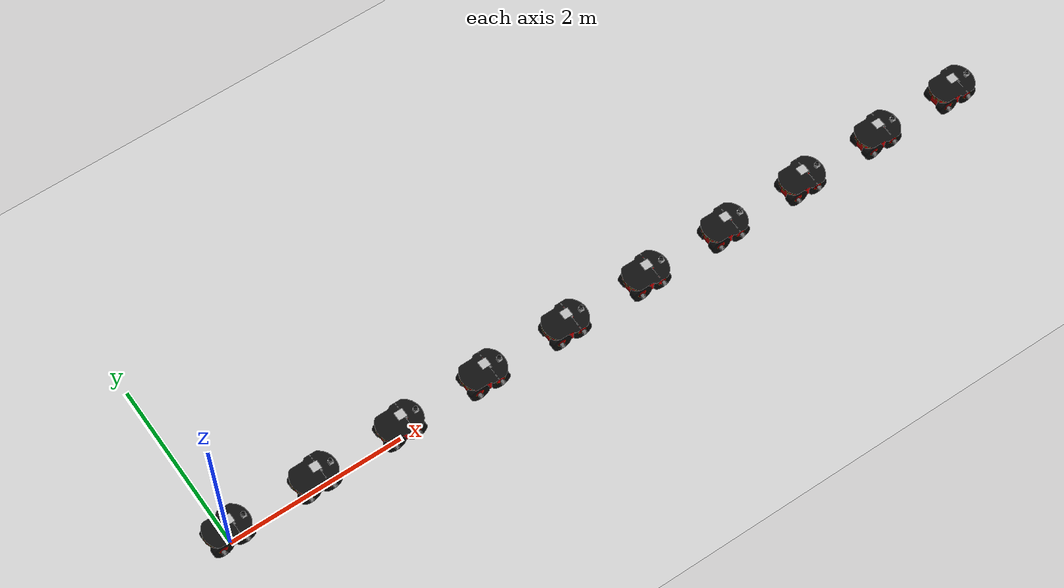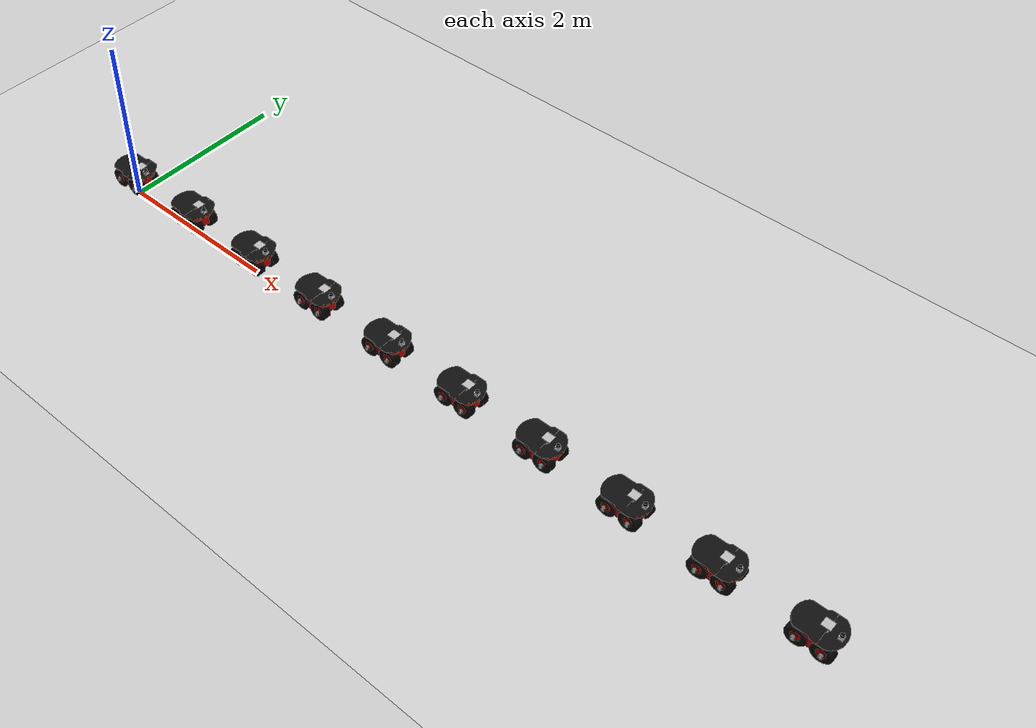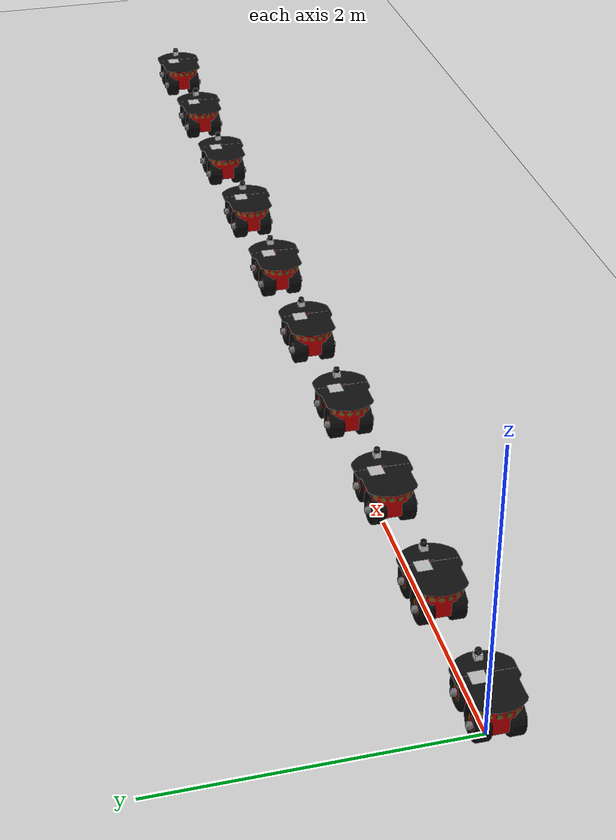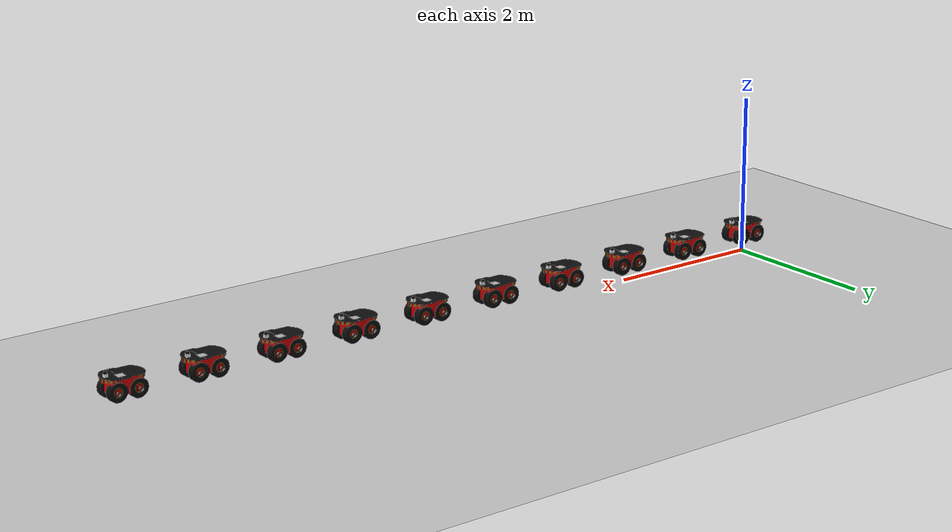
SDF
<sdf version="1.4">
 <world name="default">
  <model name="ground_plane">
   <static>1</static>
   <link name="link">
    <collision name="collision">
     <geometry><plane><normal>0 0 1</normal><size>100 100</size></plane></geometry>
     <surface><friction><ode><mu>100</mu><mu2>50</mu2></ode></friction></surface>
    </collision>
    <visual name="visual">
     <cast_shadows>0</cast_shadows>
     <geometry><plane><normal>0 0 1</normal><size>100 100</size></plane></geometry>
     <material>
      <script><uri>file://media/materials/scripts/gazebo.material</uri><name>Gazebo/Grey</name></script>
     </material>
    </visual>
    <velocity_decay><linear>0</linear><angular>0</angular></velocity_decay>
   </link>
  </model>
  <light name="sun" type="directional">
   <pose>0 0 20 0 -0 0</pose>
   <diffuse>0.8 0.8 0.8 1</diffuse>
   <specular>0.2 0.2 0.2 1</specular>
   <attenuation>
    <range>1000</range>
    <constant>0.9</constant>
    <linear>0.01</linear>
    <quadratic>0.001</quadratic>
   </attenuation>
   <direction>0.5 0.1 -0.9</direction>
  </light>
  <physics type="ode">
   <max_step_size>0.001</max_step_size>
   <real_time_factor>1</real_time_factor>
   <real_time_update_rate>1000</real_time_update_rate>
   <gravity>0 0 -9.8</gravity>
  </physics>
  <scene><ambient>0.4 0.4 0.4 1</ambient><background>0.7 0.7 0.7 1</background><shadows>1</shadows></scene>
  <model name="pioneer3at_1">
   <pose>0 0 0.3 0 -0 0</pose>
   <static>0</static>
   <link name="chassis">
    <inertial>
     <mass>500</mass>
     <inertia><ixx>0.3338</ixx><ixy>0</ixy><ixz>0</ixz><iyy>0.4783</iyy><iyz>0</iyz><izz>0.3338</izz></inertia>
    </inertial>
    <collision name="collision"><geometry><box><size>0.501 0.2 0.19</size></box></geometry></collision>
    <visual name="visual">
     <geometry><mesh><uri>model://pioneer3at/meshes/chassis.dae</uri></mesh></geometry>
    </visual>
    <velocity_decay><linear>0</linear><angular>0</angular></velocity_decay>
   </link>
   <link name="right_front_wheel">
    <pose>0.125 -0.1005 -0.06 1.5707 -0 0</pose>
    <collision name="collision">
     <geometry><cylinder><radius>0.11</radius><length>0.075</length></cylinder></geometry>
     <surface><friction><ode><mu>1</mu><mu2>1</mu2><slip1>0.5</slip1><slip2>0</slip2></ode></friction></surface>
    </collision>
    <visual name="visual">
     <geometry><mesh><uri>model://pioneer3at/meshes/wheel.dae</uri></mesh></geometry>
    </visual>
    <velocity_decay><linear>0</linear><angular>0</angular></velocity_decay>
    <inertial>
     <inertia><ixx>1</ixx><ixy>0</ixy><ixz>0</ixz><iyy>1</iyy><iyz>0</iyz><izz>1</izz></inertia>
     <mass>1</mass>
    </inertial>
   </link>
   <link name="left_front_wheel">
    <pose>0.125 0.1005 -0.06 1.5707 -0 0</pose>
    <collision name="collision">
     <geometry><cylinder><radius>0.11</radius><length>0.075</length></cylinder></geometry>
     <surface><friction><ode><mu>1</mu><mu2>1</mu2><slip1>0.5</slip1><slip2>0</slip2></ode></friction></surface>
    </collision>
    <visual name="visual">
     <geometry><mesh><uri>model://pioneer3at/meshes/wheel.dae</uri></mesh></geometry>
    </visual>
    <velocity_decay><linear>0</linear><angular>0</angular></velocity_decay>
    <inertial>
     <inertia><ixx>1</ixx><ixy>0</ixy><ixz>0</ixz><iyy>1</iyy><iyz>0</iyz><izz>1</izz></inertia>
     <mass>1</mass>
    </inertial>
   </link>
   <link name="right_rear_wheel">
    <pose>-0.125 -0.1005 -0.06 1.5707 -0 0</pose>
    <collision name="collision">
     <geometry><cylinder><radius>0.11</radius><length>0.075</length></cylinder></geometry>
     <surface><friction><ode><mu>1</mu><mu2>1</mu2><slip1>0.5</slip1><slip2>0</slip2></ode></friction></surface>
    </collision>
    <visual name="visual">
     <geometry><mesh><uri>model://pioneer3at/meshes/wheel.dae</uri></mesh></geometry>
    </visual>
    <velocity_decay><linear>0</linear><angular>0</angular></velocity_decay>
    <inertial>
     <inertia><ixx>1</ixx><ixy>0</ixy><ixz>0</ixz><iyy>1</iyy><iyz>0</iyz><izz>1</izz></inertia>
     <mass>1</mass>
    </inertial>
   </link>
   <link name="left_rear_wheel">
    <pose>-0.125 0.1005 -0.06 1.5707 -0 0</pose>
    <collision name="collision">
     <geometry><cylinder><radius>0.11</radius><length>0.075</length></cylinder></geometry>
     <surface><friction><ode><mu>1</mu><mu2>1</mu2><slip1>0.5</slip1><slip2>0</slip2></ode></friction></surface>
    </collision>
    <visual name="visual">
     <geometry><mesh><scale>1 1 1</scale><uri>model://pioneer3at/meshes/wheel.dae</uri></mesh></geometry>
    </visual>
    <velocity_decay><linear>0</linear><angular>0</angular></velocity_decay>
    <inertial>
     <inertia><ixx>1</ixx><ixy>0</ixy><ixz>0</ixz><iyy>1</iyy><iyz>0</iyz><izz>1</izz></inertia>
     <mass>1</mass>
    </inertial>
   </link>
   <joint name="right_front" type="revolute">
    <child>right_front_wheel</child>
    <parent>chassis</parent>
    <axis><xyz>0 1 0</xyz><limit><lower>-1e+16</lower><upper>1e+16</upper></limit></axis>
   </joint>
   <joint name="right_rear" type="revolute">
    <child>right_rear_wheel</child>
    <parent>chassis</parent>
    <axis><xyz>0 1 0</xyz><limit><lower>-1e+16</lower><upper>1e+16</upper></limit></axis>
   </joint>
   <joint name="left_front" type="revolute">
    <child>left_front_wheel</child>
    <parent>chassis</parent>
    <axis><xyz>0 1 0</xyz><limit><lower>-1e+16</lower><upper>1e+16</upper></limit></axis>
   </joint>
   <joint name="left_rear" type="revolute">
    <child>left_rear_wheel</child>
    <parent>chassis</parent>
    <axis><xyz>0 1 0</xyz><limit><lower>-1e+16</lower><upper>1e+16</upper></limit></axis>
   </joint>
   <link name="hokuyo::link">
    <inertial>
     <mass>0.1</mass>
     <inertia><ixx>1</ixx><ixy>0</ixy><ixz>0</ixz><iyy>1</iyy><iyz>0</iyz><izz>1</izz></inertia>
    </inertial>
    <visual name="visual"><geometry><mesh><uri>model://hokuyo/meshes/hokuyo.dae</uri></mesh></geometry></visual>
    <collision name="collision-base">
     <pose>0 0 -0.0145 0 -0 0</pose>
     <geometry><box><size>0.05 0.05 0.041</size></box></geometry>
    </collision>
    <collision name="collision-top">
     <pose>0 0 0.0205 0 -0 0</pose>
     <geometry><cylinder><radius>0.021</radius><length>0.029</length></cylinder></geometry>
    </collision>
    <sensor name="laser" type="ray">
     <pose>0.15 0 -0.1 0 -0 0</pose>
     <ray>
      <scan>
       <horizontal>
        <samples>1040</samples>
        <resolution>1</resolution>
        <min_angle>-2.26889</min_angle>
        <max_angle>2.2689</max_angle>
       </horizontal>
      </scan>
      <range><min>0.1</min><max>30</max><resolution>0.01</resolution></range>
     </ray>
     <plugin name="gazebo_ros_hokuyo_laser_controller" filename="libgazebo_ros_laser.so">
      <gaussianNoise>0.01</gaussianNoise>
      <alwaysOn>true</alwaysOn>
      <hokuyoMinIntensity>101</hokuyoMinIntensity>
      <updateRate>40.0</updateRate>
      <topicName>/pioneer_1/scan</topicName>
      <frameName>laser</frameName>
     </plugin>
     <always_on>1</always_on>
     <update_rate>30</update_rate>
     <visualize>1</visualize>
    </sensor>
    <velocity_decay><linear>0</linear><angular>0</angular></velocity_decay>
    <pose>0.2 0 0.13 0 -0 0</pose>
   </link>
   <joint name="hokuyo_joint" type="revolute">
    <child>hokuyo::link</child>
    <parent>chassis</parent>
    <axis><xyz>0 0 1</xyz><limit><upper>0</upper><lower>0</lower></limit></axis>
   </joint>
   <link name="camera::link">
    <pose>0.05 0.05 0.05 0 -0 0</pose>
    <inertial>
     <mass>0.1</mass>
     <inertia><ixx>1</ixx><ixy>0</ixy><ixz>0</ixz><iyy>1</iyy><iyz>0</iyz><izz>1</izz></inertia>
    </inertial>
    <collision name="collision"><geometry><box><size>0.1 0.1 0.1</size></box></geometry></collision>
    <visual name="visual"><geometry><box><size>0.1 0.1 0.1</size></box></geometry></visual>
    <sensor name="camera" type="camera">
     <camera name="__default__">
      <horizontal_fov>0.752</horizontal_fov>
      <image><width>640</width><height>480</height></image>
      <clip><near>0.1</near><far>100</far></clip>
     </camera>
     <always_on>1</always_on>
     <update_rate>15</update_rate>
     <visualize>0</visualize>
     <plugin name="ros_camera" filename="libgazebo_ros_camera.so">
      <robotNamespace>/pioneer_1</robotNamespace>
     </plugin>
    </sensor>
    <velocity_decay><linear>0</linear><angular>0</angular></velocity_decay>
   </link>
   <joint name="camera_joint" type="revolute">
    <child>camera::link</child>
    <parent>chassis</parent>
    <axis><xyz>0 0 1</xyz><limit><upper>0</upper><lower>0</lower></limit></axis>
   </joint>
   <plugin name="skid_steer_drive_controller" filename="libgazebo_ros_skid_steer_drive.so">
    <updateRate>100.0</updateRate>
    <robotNamespace>/pioneer_1</robotNamespace>
    <leftFrontJoint>left_front</leftFrontJoint>
    <rightFrontJoint>right_front</rightFrontJoint>
    <leftRearJoint>left_rear</leftRearJoint>
    <rightRearJoint>right_rear</rightRearJoint>
    <wheelSeparation>0.4</wheelSeparation>
    <wheelDiameter>0.215</wheelDiameter>
    <robotBaseFrame>/pioneer_1/odom_tf</robotBaseFrame>
    <torque>120</torque>
    <commandTopic>cmd_vel</commandTopic>
    <broadcastTF>1</broadcastTF>
   </plugin>
   <plugin name="imu_en_ros" filename="libgazebo_ros_imu.so">
    <bodyName>chassis</bodyName>
    <robotNamespace>/pioneer_1</robotNamespace>
    <topicName>imu</topicName>
    <gaussianNoise>0.00</gaussianNoise>
    <updateRate>45.0</updateRate>
   </plugin>
  </model>
  <model name="pioneer3at_2">
   <pose>1 0 0.3 0 -0 0</pose>
   <static>0</static>
   <link name="chassis">
    <inertial>
     <mass>500</mass>
     <inertia><ixx>0.3338</ixx><ixy>0</ixy><ixz>0</ixz><iyy>0.4783</iyy><iyz>0</iyz><izz>0.3338</izz></inertia>
    </inertial>
    <collision name="collision"><geometry><box><size>0.501 0.2 0.19</size></box></geometry></collision>
    <visual name="visual">
     <geometry><mesh><uri>model://pioneer3at/meshes/chassis.dae</uri></mesh></geometry>
    </visual>
    <velocity_decay><linear>0</linear><angular>0</angular></velocity_decay>
   </link>
   <link name="right_front_wheel">
    <pose>0.125 -0.1005 -0.06 1.5707 -0 0</pose>
    <collision name="collision">
     <geometry><cylinder><radius>0.11</radius><length>0.075</length></cylinder></geometry>
     <surface><friction><ode><mu>1</mu><mu2>1</mu2><slip1>0.5</slip1><slip2>0</slip2></ode></friction></surface>
    </collision>
    <visual name="visual">
     <geometry><mesh><uri>model://pioneer3at/meshes/wheel.dae</uri></mesh></geometry>
    </visual>
    <velocity_decay><linear>0</linear><angular>0</angular></velocity_decay>
    <inertial>
     <inertia><ixx>1</ixx><ixy>0</ixy><ixz>0</ixz><iyy>1</iyy><iyz>0</iyz><izz>1</izz></inertia>
     <mass>1</mass>
    </inertial>
   </link>
   <link name="left_front_wheel">
    <pose>0.125 0.1005 -0.06 1.5707 -0 0</pose>
    <collision name="collision">
     <geometry><cylinder><radius>0.11</radius><length>0.075</length></cylinder></geometry>
     <surface><friction><ode><mu>1</mu><mu2>1</mu2><slip1>0.5</slip1><slip2>0</slip2></ode></friction></surface>
    </collision>
    <visual name="visual">
     <geometry><mesh><uri>model://pioneer3at/meshes/wheel.dae</uri></mesh></geometry>
    </visual>
    <velocity_decay><linear>0</linear><angular>0</angular></velocity_decay>
    <inertial>
     <inertia><ixx>1</ixx><ixy>0</ixy><ixz>0</ixz><iyy>1</iyy><iyz>0</iyz><izz>1</izz></inertia>
     <mass>1</mass>
    </inertial>
   </link>
   <link name="right_rear_wheel">
    <pose>-0.125 -0.1005 -0.06 1.5707 -0 0</pose>
    <collision name="collision">
     <geometry><cylinder><radius>0.11</radius><length>0.075</length></cylinder></geometry>
     <surface><friction><ode><mu>1</mu><mu2>1</mu2><slip1>0.5</slip1><slip2>0</slip2></ode></friction></surface>
    </collision>
    <visual name="visual">
     <geometry><mesh><uri>model://pioneer3at/meshes/wheel.dae</uri></mesh></geometry>
    </visual>
    <velocity_decay><linear>0</linear><angular>0</angular></velocity_decay>
    <inertial>
     <inertia><ixx>1</ixx><ixy>0</ixy><ixz>0</ixz><iyy>1</iyy><iyz>0</iyz><izz>1</izz></inertia>
     <mass>1</mass>
    </inertial>
   </link>
   <link name="left_rear_wheel">
    <pose>-0.125 0.1005 -0.06 1.5707 -0 0</pose>
    <collision name="collision">
     <geometry><cylinder><radius>0.11</radius><length>0.075</length></cylinder></geometry>
     <surface><friction><ode><mu>1</mu><mu2>1</mu2><slip1>0.5</slip1><slip2>0</slip2></ode></friction></surface>
    </collision>
    <visual name="visual">
     <geometry><mesh><scale>1 1 1</scale><uri>model://pioneer3at/meshes/wheel.dae</uri></mesh></geometry>
    </visual>
    <velocity_decay><linear>0</linear><angular>0</angular></velocity_decay>
    <inertial>
     <inertia><ixx>1</ixx><ixy>0</ixy><ixz>0</ixz><iyy>1</iyy><iyz>0</iyz><izz>1</izz></inertia>
     <mass>1</mass>
    </inertial>
   </link>
   <joint name="right_front" type="revolute">
    <child>right_front_wheel</child>
    <parent>chassis</parent>
    <axis><xyz>0 1 0</xyz><limit><lower>-1e+16</lower><upper>1e+16</upper></limit></axis>
   </joint>
   <joint name="right_rear" type="revolute">
    <child>right_rear_wheel</child>
    <parent>chassis</parent>
    <axis><xyz>0 1 0</xyz><limit><lower>-1e+16</lower><upper>1e+16</upper></limit></axis>
   </joint>
   <joint name="left_front" type="revolute">
    <child>left_front_wheel</child>
    <parent>chassis</parent>
    <axis><xyz>0 1 0</xyz><limit><lower>-1e+16</lower><upper>1e+16</upper></limit></axis>
   </joint>
   <joint name="left_rear" type="revolute">
    <child>left_rear_wheel</child>
    <parent>chassis</parent>
    <axis><xyz>0 1 0</xyz><limit><lower>-1e+16</lower><upper>1e+16</upper></limit></axis>
   </joint>
   <link name="hokuyo::link">
    <inertial>
     <mass>0.1</mass>
     <inertia><ixx>1</ixx><ixy>0</ixy><ixz>0</ixz><iyy>1</iyy><iyz>0</iyz><izz>1</izz></inertia>
    </inertial>
    <visual name="visual"><geometry><mesh><uri>model://hokuyo/meshes/hokuyo.dae</uri></mesh></geometry></visual>
    <collision name="collision-base">
     <pose>0 0 -0.0145 0 -0 0</pose>
     <geometry><box><size>0.05 0.05 0.041</size></box></geometry>
    </collision>
    <collision name="collision-top">
     <pose>0 0 0.0205 0 -0 0</pose>
     <geometry><cylinder><radius>0.021</radius><length>0.029</length></cylinder></geometry>
    </collision>
    <sensor name="laser" type="ray">
     <pose>0.15 0 -0.1 0 -0 0</pose>
     <ray>
      <scan>
       <horizontal>
        <samples>1040</samples>
        <resolution>1</resolution>
        <min_angle>-2.26889</min_angle>
        <max_angle>2.2689</max_angle>
       </horizontal>
      </scan>
      <range><min>0.1</min><max>30</max><resolution>0.01</resolution></range>
     </ray>
     <plugin name="gazebo_ros_hokuyo_laser_controller" filename="libgazebo_ros_laser.so">
      <gaussianNoise>0.01</gaussianNoise>
      <alwaysOn>true</alwaysOn>
      <hokuyoMinIntensity>101</hokuyoMinIntensity>
      <updateRate>40.0</updateRate>
      <topicName>/pioneer_2/scan</topicName>
      <frameName>laser</frameName>
     </plugin>
     <always_on>1</always_on>
     <update_rate>30</update_rate>
     <visualize>1</visualize>
    </sensor>
    <velocity_decay><linear>0</linear><angular>0</angular></velocity_decay>
    <pose>0.2 0 0.13 0 -0 0</pose>
   </link>
   <joint name="hokuyo_joint" type="revolute">
    <child>hokuyo::link</child>
    <parent>chassis</parent>
    <axis><xyz>0 0 1</xyz><limit><upper>0</upper><lower>0</lower></limit></axis>
   </joint>
   <link name="camera::link">
    <pose>0.05 0.05 0.05 0 -0 0</pose>
    <inertial>
     <mass>0.1</mass>
     <inertia><ixx>1</ixx><ixy>0</ixy><ixz>0</ixz><iyy>1</iyy><iyz>0</iyz><izz>1</izz></inertia>
    </inertial>
    <collision name="collision"><geometry><box><size>0.1 0.1 0.1</size></box></geometry></collision>
    <visual name="visual"><geometry><box><size>0.1 0.1 0.1</size></box></geometry></visual>
    <sensor name="camera" type="camera">
     <camera name="__default__">
      <horizontal_fov>0.752</horizontal_fov>
      <image><width>640</width><height>480</height></image>
      <clip><near>0.1</near><far>100</far></clip>
     </camera>
     <always_on>1</always_on>
     <update_rate>15</update_rate>
     <visualize>0</visualize>
     <plugin name="ros_camera" filename="libgazebo_ros_camera.so">
      <robotNamespace>/pioneer_2</robotNamespace>
     </plugin>
    </sensor>
    <velocity_decay><linear>0</linear><angular>0</angular></velocity_decay>
   </link>
   <joint name="camera_joint" type="revolute">
    <child>camera::link</child>
    <parent>chassis</parent>
    <axis><xyz>0 0 1</xyz><limit><upper>0</upper><lower>0</lower></limit></axis>
   </joint>
   <plugin name="skid_steer_drive_controller" filename="libgazebo_ros_skid_steer_drive.so">
    <updateRate>100.0</updateRate>
    <robotNamespace>/pioneer_2</robotNamespace>
    <leftFrontJoint>left_front</leftFrontJoint>
    <rightFrontJoint>right_front</rightFrontJoint>
    <leftRearJoint>left_rear</leftRearJoint>
    <rightRearJoint>right_rear</rightRearJoint>
    <wheelSeparation>0.4</wheelSeparation>
    <wheelDiameter>0.215</wheelDiameter>
    <robotBaseFrame>/pioneer_2/odom_tf</robotBaseFrame>
    <torque>120</torque>
    <commandTopic>cmd_vel</commandTopic>
    <broadcastTF>1</broadcastTF>
   </plugin>
   <plugin name="imu_en_ros" filename="libgazebo_ros_imu.so">
    <bodyName>chassis</bodyName>
    <robotNamespace>/pioneer_2</robotNamespace>
    <topicName>imu</topicName>
    <gaussianNoise>0.00</gaussianNoise>
    <updateRate>45.0</updateRate>
   </plugin>
  </model>
  <model name="pioneer3at_3">
   <pose>2 0 0.3 0 -0 0</pose>
   <static>0</static>
   <link name="chassis">
    <inertial>
     <mass>500</mass>
     <inertia><ixx>0.3338</ixx><ixy>0</ixy><ixz>0</ixz><iyy>0.4783</iyy><iyz>0</iyz><izz>0.3338</izz></inertia>
    </inertial>
    <collision name="collision"><geometry><box><size>0.501 0.2 0.19</size></box></geometry></collision>
    <visual name="visual">
     <geometry><mesh><uri>model://pioneer3at/meshes/chassis.dae</uri></mesh></geometry>
    </visual>
    <velocity_decay><linear>0</linear><angular>0</angular></velocity_decay>
   </link>
   <link name="right_front_wheel">
    <pose>0.125 -0.1005 -0.06 1.5707 -0 0</pose>
    <collision name="collision">
     <geometry><cylinder><radius>0.11</radius><length>0.075</length></cylinder></geometry>
     <surface><friction><ode><mu>1</mu><mu2>1</mu2><slip1>0.5</slip1><slip2>0</slip2></ode></friction></surface>
    </collision>
    <visual name="visual">
     <geometry><mesh><uri>model://pioneer3at/meshes/wheel.dae</uri></mesh></geometry>
    </visual>
    <velocity_decay><linear>0</linear><angular>0</angular></velocity_decay>
    <inertial>
     <inertia><ixx>1</ixx><ixy>0</ixy><ixz>0</ixz><iyy>1</iyy><iyz>0</iyz><izz>1</izz></inertia>
     <mass>1</mass>
    </inertial>
   </link>
   <link name="left_front_wheel">
    <pose>0.125 0.1005 -0.06 1.5707 -0 0</pose>
    <collision name="collision">
     <geometry><cylinder><radius>0.11</radius><length>0.075</length></cylinder></geometry>
     <surface><friction><ode><mu>1</mu><mu2>1</mu2><slip1>0.5</slip1><slip2>0</slip2></ode></friction></surface>
    </collision>
    <visual name="visual">
     <geometry><mesh><uri>model://pioneer3at/meshes/wheel.dae</uri></mesh></geometry>
    </visual>
    <velocity_decay><linear>0</linear><angular>0</angular></velocity_decay>
    <inertial>
     <inertia><ixx>1</ixx><ixy>0</ixy><ixz>0</ixz><iyy>1</iyy><iyz>0</iyz><izz>1</izz></inertia>
     <mass>1</mass>
    </inertial>
   </link>
   <link name="right_rear_wheel">
    <pose>-0.125 -0.1005 -0.06 1.5707 -0 0</pose>
    <collision name="collision">
     <geometry><cylinder><radius>0.11</radius><length>0.075</length></cylinder></geometry>
     <surface><friction><ode><mu>1</mu><mu2>1</mu2><slip1>0.5</slip1><slip2>0</slip2></ode></friction></surface>
    </collision>
    <visual name="visual">
     <geometry><mesh><uri>model://pioneer3at/meshes/wheel.dae</uri></mesh></geometry>
    </visual>
    <velocity_decay><linear>0</linear><angular>0</angular></velocity_decay>
    <inertial>
     <inertia><ixx>1</ixx><ixy>0</ixy><ixz>0</ixz><iyy>1</iyy><iyz>0</iyz><izz>1</izz></inertia>
     <mass>1</mass>
    </inertial>
   </link>
   <link name="left_rear_wheel">
    <pose>-0.125 0.1005 -0.06 1.5707 -0 0</pose>
    <collision name="collision">
     <geometry><cylinder><radius>0.11</radius><length>0.075</length></cylinder></geometry>
     <surface><friction><ode><mu>1</mu><mu2>1</mu2><slip1>0.5</slip1><slip2>0</slip2></ode></friction></surface>
    </collision>
    <visual name="visual">
     <geometry><mesh><scale>1 1 1</scale><uri>model://pioneer3at/meshes/wheel.dae</uri></mesh></geometry>
    </visual>
    <velocity_decay><linear>0</linear><angular>0</angular></velocity_decay>
    <inertial>
     <inertia><ixx>1</ixx><ixy>0</ixy><ixz>0</ixz><iyy>1</iyy><iyz>0</iyz><izz>1</izz></inertia>
     <mass>1</mass>
    </inertial>
   </link>
   <joint name="right_front" type="revolute">
    <child>right_front_wheel</child>
    <parent>chassis</parent>
    <axis><xyz>0 1 0</xyz><limit><lower>-1e+16</lower><upper>1e+16</upper></limit></axis>
   </joint>
   <joint name="right_rear" type="revolute">
    <child>right_rear_wheel</child>
    <parent>chassis</parent>
    <axis><xyz>0 1 0</xyz><limit><lower>-1e+16</lower><upper>1e+16</upper></limit></axis>
   </joint>
   <joint name="left_front" type="revolute">
    <child>left_front_wheel</child>
    <parent>chassis</parent>
    <axis><xyz>0 1 0</xyz><limit><lower>-1e+16</lower><upper>1e+16</upper></limit></axis>
   </joint>
   <joint name="left_rear" type="revolute">
    <child>left_rear_wheel</child>
    <parent>chassis</parent>
    <axis><xyz>0 1 0</xyz><limit><lower>-1e+16</lower><upper>1e+16</upper></limit></axis>
   </joint>
   <link name="hokuyo::link">
    <inertial>
     <mass>0.1</mass>
     <inertia><ixx>1</ixx><ixy>0</ixy><ixz>0</ixz><iyy>1</iyy><iyz>0</iyz><izz>1</izz></inertia>
    </inertial>
    <visual name="visual"><geometry><mesh><uri>model://hokuyo/meshes/hokuyo.dae</uri></mesh></geometry></visual>
    <collision name="collision-base">
     <pose>0 0 -0.0145 0 -0 0</pose>
     <geometry><box><size>0.05 0.05 0.041</size></box></geometry>
    </collision>
    <collision name="collision-top">
     <pose>0 0 0.0205 0 -0 0</pose>
     <geometry><cylinder><radius>0.021</radius><length>0.029</length></cylinder></geometry>
    </collision>
    <sensor name="laser" type="ray">
     <pose>0.15 0 -0.1 0 -0 0</pose>
     <ray>
      <scan>
       <horizontal>
        <samples>1040</samples>
        <resolution>1</resolution>
        <min_angle>-2.26889</min_angle>
        <max_angle>2.2689</max_angle>
       </horizontal>
      </scan>
      <range><min>0.1</min><max>30</max><resolution>0.01</resolution></range>
     </ray>
     <plugin name="gazebo_ros_hokuyo_laser_controller" filename="libgazebo_ros_laser.so">
      <gaussianNoise>0.01</gaussianNoise>
      <alwaysOn>true</alwaysOn>
      <hokuyoMinIntensity>101</hokuyoMinIntensity>
      <updateRate>40.0</updateRate>
      <topicName>/pioneer_3/scan</topicName>
      <frameName>laser</frameName>
     </plugin>
     <always_on>1</always_on>
     <update_rate>30</update_rate>
     <visualize>1</visualize>
    </sensor>
    <velocity_decay><linear>0</linear><angular>0</angular></velocity_decay>
    <pose>0.2 0 0.13 0 -0 0</pose>
   </link>
   <joint name="hokuyo_joint" type="revolute">
    <child>hokuyo::link</child>
    <parent>chassis</parent>
    <axis><xyz>0 0 1</xyz><limit><upper>0</upper><lower>0</lower></limit></axis>
   </joint>
   <link name="camera::link">
    <pose>0.05 0.05 0.05 0 -0 0</pose>
    <inertial>
     <mass>0.1</mass>
     <inertia><ixx>1</ixx><ixy>0</ixy><ixz>0</ixz><iyy>1</iyy><iyz>0</iyz><izz>1</izz></inertia>
    </inertial>
    <collision name="collision"><geometry><box><size>0.1 0.1 0.1</size></box></geometry></collision>
    <visual name="visual"><geometry><box><size>0.1 0.1 0.1</size></box></geometry></visual>
    <sensor name="camera" type="camera">
     <camera name="__default__">
      <horizontal_fov>0.752</horizontal_fov>
      <image><width>640</width><height>480</height></image>
      <clip><near>0.1</near><far>100</far></clip>
     </camera>
     <always_on>1</always_on>
     <update_rate>15</update_rate>
     <visualize>0</visualize>
     <plugin name="ros_camera" filename="libgazebo_ros_camera.so">
      <robotNamespace>/pioneer_3</robotNamespace>
     </plugin>
    </sensor>
    <velocity_decay><linear>0</linear><angular>0</angular></velocity_decay>
   </link>
   <joint name="camera_joint" type="revolute">
    <child>camera::link</child>
    <parent>chassis</parent>
    <axis><xyz>0 0 1</xyz><limit><upper>0</upper><lower>0</lower></limit></axis>
   </joint>
   <plugin name="skid_steer_drive_controller" filename="libgazebo_ros_skid_steer_drive.so">
    <updateRate>100.0</updateRate>
    <robotNamespace>/pioneer_3</robotNamespace>
    <leftFrontJoint>left_front</leftFrontJoint>
    <rightFrontJoint>right_front</rightFrontJoint>
    <leftRearJoint>left_rear</leftRearJoint>
    <rightRearJoint>right_rear</rightRearJoint>
    <wheelSeparation>0.4</wheelSeparation>
    <wheelDiameter>0.215</wheelDiameter>
    <robotBaseFrame>/pioneer_3/odom_tf</robotBaseFrame>
    <torque>120</torque>
    <commandTopic>cmd_vel</commandTopic>
    <broadcastTF>1</broadcastTF>
   </plugin>
   <plugin name="imu_en_ros" filename="libgazebo_ros_imu.so">
    <bodyName>chassis</bodyName>
    <robotNamespace>/pioneer_3</robotNamespace>
    <topicName>imu</topicName>
    <gaussianNoise>0.00</gaussianNoise>
    <updateRate>45.0</updateRate>
   </plugin>
  </model>
  <model name="pioneer3at_4">
   <pose>3 0 0.3 0 -0 0</pose>
   <static>0</static>
   <link name="chassis">
    <inertial>
     <mass>500</mass>
     <inertia><ixx>0.3338</ixx><ixy>0</ixy><ixz>0</ixz><iyy>0.4783</iyy><iyz>0</iyz><izz>0.3338</izz></inertia>
    </inertial>
    <collision name="collision"><geometry><box><size>0.501 0.2 0.19</size></box></geometry></collision>
    <visual name="visual">
     <geometry><mesh><uri>model://pioneer3at/meshes/chassis.dae</uri></mesh></geometry>
    </visual>
    <velocity_decay><linear>0</linear><angular>0</angular></velocity_decay>
   </link>
   <link name="right_front_wheel">
    <pose>0.125 -0.1005 -0.06 1.5707 -0 0</pose>
    <collision name="collision">
     <geometry><cylinder><radius>0.11</radius><length>0.075</length></cylinder></geometry>
     <surface><friction><ode><mu>1</mu><mu2>1</mu2><slip1>0.5</slip1><slip2>0</slip2></ode></friction></surface>
    </collision>
    <visual name="visual">
     <geometry><mesh><uri>model://pioneer3at/meshes/wheel.dae</uri></mesh></geometry>
    </visual>
    <velocity_decay><linear>0</linear><angular>0</angular></velocity_decay>
    <inertial>
     <inertia><ixx>1</ixx><ixy>0</ixy><ixz>0</ixz><iyy>1</iyy><iyz>0</iyz><izz>1</izz></inertia>
     <mass>1</mass>
    </inertial>
   </link>
   <link name="left_front_wheel">
    <pose>0.125 0.1005 -0.06 1.5707 -0 0</pose>
    <collision name="collision">
     <geometry><cylinder><radius>0.11</radius><length>0.075</length></cylinder></geometry>
     <surface><friction><ode><mu>1</mu><mu2>1</mu2><slip1>0.5</slip1><slip2>0</slip2></ode></friction></surface>
    </collision>
    <visual name="visual">
     <geometry><mesh><uri>model://pioneer3at/meshes/wheel.dae</uri></mesh></geometry>
    </visual>
    <velocity_decay><linear>0</linear><angular>0</angular></velocity_decay>
    <inertial>
     <inertia><ixx>1</ixx><ixy>0</ixy><ixz>0</ixz><iyy>1</iyy><iyz>0</iyz><izz>1</izz></inertia>
     <mass>1</mass>
    </inertial>
   </link>
   <link name="right_rear_wheel">
    <pose>-0.125 -0.1005 -0.06 1.5707 -0 0</pose>
    <collision name="collision">
     <geometry><cylinder><radius>0.11</radius><length>0.075</length></cylinder></geometry>
     <surface><friction><ode><mu>1</mu><mu2>1</mu2><slip1>0.5</slip1><slip2>0</slip2></ode></friction></surface>
    </collision>
    <visual name="visual">
     <geometry><mesh><uri>model://pioneer3at/meshes/wheel.dae</uri></mesh></geometry>
    </visual>
    <velocity_decay><linear>0</linear><angular>0</angular></velocity_decay>
    <inertial>
     <inertia><ixx>1</ixx><ixy>0</ixy><ixz>0</ixz><iyy>1</iyy><iyz>0</iyz><izz>1</izz></inertia>
     <mass>1</mass>
    </inertial>
   </link>
   <link name="left_rear_wheel">
    <pose>-0.125 0.1005 -0.06 1.5707 -0 0</pose>
    <collision name="collision">
     <geometry><cylinder><radius>0.11</radius><length>0.075</length></cylinder></geometry>
     <surface><friction><ode><mu>1</mu><mu2>1</mu2><slip1>0.5</slip1><slip2>0</slip2></ode></friction></surface>
    </collision>
    <visual name="visual">
     <geometry><mesh><scale>1 1 1</scale><uri>model://pioneer3at/meshes/wheel.dae</uri></mesh></geometry>
    </visual>
    <velocity_decay><linear>0</linear><angular>0</angular></velocity_decay>
    <inertial>
     <inertia><ixx>1</ixx><ixy>0</ixy><ixz>0</ixz><iyy>1</iyy><iyz>0</iyz><izz>1</izz></inertia>
     <mass>1</mass>
    </inertial>
   </link>
   <joint name="right_front" type="revolute">
    <child>right_front_wheel</child>
    <parent>chassis</parent>
    <axis><xyz>0 1 0</xyz><limit><lower>-1e+16</lower><upper>1e+16</upper></limit></axis>
   </joint>
   <joint name="right_rear" type="revolute">
    <child>right_rear_wheel</child>
    <parent>chassis</parent>
    <axis><xyz>0 1 0</xyz><limit><lower>-1e+16</lower><upper>1e+16</upper></limit></axis>
   </joint>
   <joint name="left_front" type="revolute">
    <child>left_front_wheel</child>
    <parent>chassis</parent>
    <axis><xyz>0 1 0</xyz><limit><lower>-1e+16</lower><upper>1e+16</upper></limit></axis>
   </joint>
   <joint name="left_rear" type="revolute">
    <child>left_rear_wheel</child>
    <parent>chassis</parent>
    <axis><xyz>0 1 0</xyz><limit><lower>-1e+16</lower><upper>1e+16</upper></limit></axis>
   </joint>
   <link name="hokuyo::link">
    <inertial>
     <mass>0.1</mass>
     <inertia><ixx>1</ixx><ixy>0</ixy><ixz>0</ixz><iyy>1</iyy><iyz>0</iyz><izz>1</izz></inertia>
    </inertial>
    <visual name="visual"><geometry><mesh><uri>model://hokuyo/meshes/hokuyo.dae</uri></mesh></geometry></visual>
    <collision name="collision-base">
     <pose>0 0 -0.0145 0 -0 0</pose>
     <geometry><box><size>0.05 0.05 0.041</size></box></geometry>
    </collision>
    <collision name="collision-top">
     <pose>0 0 0.0205 0 -0 0</pose>
     <geometry><cylinder><radius>0.021</radius><length>0.029</length></cylinder></geometry>
    </collision>
    <sensor name="laser" type="ray">
     <pose>0.15 0 -0.1 0 -0 0</pose>
     <ray>
      <scan>
       <horizontal>
        <samples>1040</samples>
        <resolution>1</resolution>
        <min_angle>-2.26889</min_angle>
        <max_angle>2.2689</max_angle>
       </horizontal>
      </scan>
      <range><min>0.1</min><max>30</max><resolution>0.01</resolution></range>
     </ray>
     <plugin name="gazebo_ros_hokuyo_laser_controller" filename="libgazebo_ros_laser.so">
      <gaussianNoise>0.01</gaussianNoise>
      <alwaysOn>true</alwaysOn>
      <hokuyoMinIntensity>101</hokuyoMinIntensity>
      <updateRate>40.0</updateRate>
      <topicName>/pioneer_4/scan</topicName>
      <frameName>laser</frameName>
     </plugin>
     <always_on>1</always_on>
     <update_rate>30</update_rate>
     <visualize>1</visualize>
    </sensor>
    <velocity_decay><linear>0</linear><angular>0</angular></velocity_decay>
    <pose>0.2 0 0.13 0 -0 0</pose>
   </link>
   <joint name="hokuyo_joint" type="revolute">
    <child>hokuyo::link</child>
    <parent>chassis</parent>
    <axis><xyz>0 0 1</xyz><limit><upper>0</upper><lower>0</lower></limit></axis>
   </joint>
   <link name="camera::link">
    <pose>0.05 0.05 0.05 0 -0 0</pose>
    <inertial>
     <mass>0.1</mass>
     <inertia><ixx>1</ixx><ixy>0</ixy><ixz>0</ixz><iyy>1</iyy><iyz>0</iyz><izz>1</izz></inertia>
    </inertial>
    <collision name="collision"><geometry><box><size>0.1 0.1 0.1</size></box></geometry></collision>
    <visual name="visual"><geometry><box><size>0.1 0.1 0.1</size></box></geometry></visual>
    <sensor name="camera" type="camera">
     <camera name="__default__">
      <horizontal_fov>0.752</horizontal_fov>
      <image><width>640</width><height>480</height></image>
      <clip><near>0.1</near><far>100</far></clip>
     </camera>
     <always_on>1</always_on>
     <update_rate>15</update_rate>
     <visualize>0</visualize>
     <plugin name="ros_camera" filename="libgazebo_ros_camera.so">
      <robotNamespace>/pioneer_4</robotNamespace>
     </plugin>
    </sensor>
    <velocity_decay><linear>0</linear><angular>0</angular></velocity_decay>
   </link>
   <joint name="camera_joint" type="revolute">
    <child>camera::link</child>
    <parent>chassis</parent>
    <axis><xyz>0 0 1</xyz><limit><upper>0</upper><lower>0</lower></limit></axis>
   </joint>
   <plugin name="skid_steer_drive_controller" filename="libgazebo_ros_skid_steer_drive.so">
    <updateRate>100.0</updateRate>
    <robotNamespace>/pioneer_4</robotNamespace>
    <leftFrontJoint>left_front</leftFrontJoint>
    <rightFrontJoint>right_front</rightFrontJoint>
    <leftRearJoint>left_rear</leftRearJoint>
    <rightRearJoint>right_rear</rightRearJoint>
    <wheelSeparation>0.4</wheelSeparation>
    <wheelDiameter>0.215</wheelDiameter>
    <robotBaseFrame>/pioneer_4/odom_tf</robotBaseFrame>
    <torque>120</torque>
    <commandTopic>cmd_vel</commandTopic>
    <broadcastTF>1</broadcastTF>
   </plugin>
   <plugin name="imu_en_ros" filename="libgazebo_ros_imu.so">
    <bodyName>chassis</bodyName>
    <robotNamespace>/pioneer_4</robotNamespace>
    <topicName>imu</topicName>
    <gaussianNoise>0.00</gaussianNoise>
    <updateRate>45.0</updateRate>
   </plugin>
  </model>
  <model name="pioneer3at_5">
   <pose>4 0 0.3 0 -0 0</pose>
   <static>0</static>
   <link name="chassis">
    <inertial>
     <mass>500</mass>
     <inertia><ixx>0.3338</ixx><ixy>0</ixy><ixz>0</ixz><iyy>0.4783</iyy><iyz>0</iyz><izz>0.3338</izz></inertia>
    </inertial>
    <collision name="collision"><geometry><box><size>0.501 0.2 0.19</size></box></geometry></collision>
    <visual name="visual">
     <geometry><mesh><uri>model://pioneer3at/meshes/chassis.dae</uri></mesh></geometry>
    </visual>
    <velocity_decay><linear>0</linear><angular>0</angular></velocity_decay>
   </link>
   <link name="right_front_wheel">
    <pose>0.125 -0.1005 -0.06 1.5707 -0 0</pose>
    <collision name="collision">
     <geometry><cylinder><radius>0.11</radius><length>0.075</length></cylinder></geometry>
     <surface><friction><ode><mu>1</mu><mu2>1</mu2><slip1>0.5</slip1><slip2>0</slip2></ode></friction></surface>
    </collision>
    <visual name="visual">
     <geometry><mesh><uri>model://pioneer3at/meshes/wheel.dae</uri></mesh></geometry>
    </visual>
    <velocity_decay><linear>0</linear><angular>0</angular></velocity_decay>
    <inertial>
     <inertia><ixx>1</ixx><ixy>0</ixy><ixz>0</ixz><iyy>1</iyy><iyz>0</iyz><izz>1</izz></inertia>
     <mass>1</mass>
    </inertial>
   </link>
   <link name="left_front_wheel">
    <pose>0.125 0.1005 -0.06 1.5707 -0 0</pose>
    <collision name="collision">
     <geometry><cylinder><radius>0.11</radius><length>0.075</length></cylinder></geometry>
     <surface><friction><ode><mu>1</mu><mu2>1</mu2><slip1>0.5</slip1><slip2>0</slip2></ode></friction></surface>
    </collision>
    <visual name="visual">
     <geometry><mesh><uri>model://pioneer3at/meshes/wheel.dae</uri></mesh></geometry>
    </visual>
    <velocity_decay><linear>0</linear><angular>0</angular></velocity_decay>
    <inertial>
     <inertia><ixx>1</ixx><ixy>0</ixy><ixz>0</ixz><iyy>1</iyy><iyz>0</iyz><izz>1</izz></inertia>
     <mass>1</mass>
    </inertial>
   </link>
   <link name="right_rear_wheel">
    <pose>-0.125 -0.1005 -0.06 1.5707 -0 0</pose>
    <collision name="collision">
     <geometry><cylinder><radius>0.11</radius><length>0.075</length></cylinder></geometry>
     <surface><friction><ode><mu>1</mu><mu2>1</mu2><slip1>0.5</slip1><slip2>0</slip2></ode></friction></surface>
    </collision>
    <visual name="visual">
     <geometry><mesh><uri>model://pioneer3at/meshes/wheel.dae</uri></mesh></geometry>
    </visual>
    <velocity_decay><linear>0</linear><angular>0</angular></velocity_decay>
    <inertial>
     <inertia><ixx>1</ixx><ixy>0</ixy><ixz>0</ixz><iyy>1</iyy><iyz>0</iyz><izz>1</izz></inertia>
     <mass>1</mass>
    </inertial>
   </link>
   <link name="left_rear_wheel">
    <pose>-0.125 0.1005 -0.06 1.5707 -0 0</pose>
    <collision name="collision">
     <geometry><cylinder><radius>0.11</radius><length>0.075</length></cylinder></geometry>
     <surface><friction><ode><mu>1</mu><mu2>1</mu2><slip1>0.5</slip1><slip2>0</slip2></ode></friction></surface>
    </collision>
    <visual name="visual">
     <geometry><mesh><scale>1 1 1</scale><uri>model://pioneer3at/meshes/wheel.dae</uri></mesh></geometry>
    </visual>
    <velocity_decay><linear>0</linear><angular>0</angular></velocity_decay>
    <inertial>
     <inertia><ixx>1</ixx><ixy>0</ixy><ixz>0</ixz><iyy>1</iyy><iyz>0</iyz><izz>1</izz></inertia>
     <mass>1</mass>
    </inertial>
   </link>
   <joint name="right_front" type="revolute">
    <child>right_front_wheel</child>
    <parent>chassis</parent>
    <axis><xyz>0 1 0</xyz><limit><lower>-1e+16</lower><upper>1e+16</upper></limit></axis>
   </joint>
   <joint name="right_rear" type="revolute">
    <child>right_rear_wheel</child>
    <parent>chassis</parent>
    <axis><xyz>0 1 0</xyz><limit><lower>-1e+16</lower><upper>1e+16</upper></limit></axis>
   </joint>
   <joint name="left_front" type="revolute">
    <child>left_front_wheel</child>
    <parent>chassis</parent>
    <axis><xyz>0 1 0</xyz><limit><lower>-1e+16</lower><upper>1e+16</upper></limit></axis>
   </joint>
   <joint name="left_rear" type="revolute">
    <child>left_rear_wheel</child>
    <parent>chassis</parent>
    <axis><xyz>0 1 0</xyz><limit><lower>-1e+16</lower><upper>1e+16</upper></limit></axis>
   </joint>
   <link name="hokuyo::link">
    <inertial>
     <mass>0.1</mass>
     <inertia><ixx>1</ixx><ixy>0</ixy><ixz>0</ixz><iyy>1</iyy><iyz>0</iyz><izz>1</izz></inertia>
    </inertial>
    <visual name="visual"><geometry><mesh><uri>model://hokuyo/meshes/hokuyo.dae</uri></mesh></geometry></visual>
    <collision name="collision-base">
     <pose>0 0 -0.0145 0 -0 0</pose>
     <geometry><box><size>0.05 0.05 0.041</size></box></geometry>
    </collision>
    <collision name="collision-top">
     <pose>0 0 0.0205 0 -0 0</pose>
     <geometry><cylinder><radius>0.021</radius><length>0.029</length></cylinder></geometry>
    </collision>
    <sensor name="laser" type="ray">
     <pose>0.15 0 -0.1 0 -0 0</pose>
     <ray>
      <scan>
       <horizontal>
        <samples>1040</samples>
        <resolution>1</resolution>
        <min_angle>-2.26889</min_angle>
        <max_angle>2.2689</max_angle>
       </horizontal>
      </scan>
      <range><min>0.1</min><max>30</max><resolution>0.01</resolution></range>
     </ray>
     <plugin name="gazebo_ros_hokuyo_laser_controller" filename="libgazebo_ros_laser.so">
      <gaussianNoise>0.01</gaussianNoise>
      <alwaysOn>true</alwaysOn>
      <hokuyoMinIntensity>101</hokuyoMinIntensity>
      <updateRate>40.0</updateRate>
      <topicName>/pioneer_5/scan</topicName>
      <frameName>laser</frameName>
     </plugin>
     <always_on>1</always_on>
     <update_rate>30</update_rate>
     <visualize>1</visualize>
    </sensor>
    <velocity_decay><linear>0</linear><angular>0</angular></velocity_decay>
    <pose>0.2 0 0.13 0 -0 0</pose>
   </link>
   <joint name="hokuyo_joint" type="revolute">
    <child>hokuyo::link</child>
    <parent>chassis</parent>
    <axis><xyz>0 0 1</xyz><limit><upper>0</upper><lower>0</lower></limit></axis>
   </joint>
   <link name="camera::link">
    <pose>0.05 0.05 0.05 0 -0 0</pose>
    <inertial>
     <mass>0.1</mass>
     <inertia><ixx>1</ixx><ixy>0</ixy><ixz>0</ixz><iyy>1</iyy><iyz>0</iyz><izz>1</izz></inertia>
    </inertial>
    <collision name="collision"><geometry><box><size>0.1 0.1 0.1</size></box></geometry></collision>
    <visual name="visual"><geometry><box><size>0.1 0.1 0.1</size></box></geometry></visual>
    <sensor name="camera" type="camera">
     <camera name="__default__">
      <horizontal_fov>0.752</horizontal_fov>
      <image><width>640</width><height>480</height></image>
      <clip><near>0.1</near><far>100</far></clip>
     </camera>
     <always_on>1</always_on>
     <update_rate>15</update_rate>
     <visualize>0</visualize>
     <plugin name="ros_camera" filename="libgazebo_ros_camera.so">
      <robotNamespace>/pioneer_5</robotNamespace>
     </plugin>
    </sensor>
    <velocity_decay><linear>0</linear><angular>0</angular></velocity_decay>
   </link>
   <joint name="camera_joint" type="revolute">
    <child>camera::link</child>
    <parent>chassis</parent>
    <axis><xyz>0 0 1</xyz><limit><upper>0</upper><lower>0</lower></limit></axis>
   </joint>
   <plugin name="skid_steer_drive_controller" filename="libgazebo_ros_skid_steer_drive.so">
    <updateRate>100.0</updateRate>
    <robotNamespace>/pioneer_5</robotNamespace>
    <leftFrontJoint>left_front</leftFrontJoint>
    <rightFrontJoint>right_front</rightFrontJoint>
    <leftRearJoint>left_rear</leftRearJoint>
    <rightRearJoint>right_rear</rightRearJoint>
    <wheelSeparation>0.4</wheelSeparation>
    <wheelDiameter>0.215</wheelDiameter>
    <robotBaseFrame>/pioneer_5/odom_tf</robotBaseFrame>
    <torque>120</torque>
    <commandTopic>cmd_vel</commandTopic>
    <broadcastTF>1</broadcastTF>
   </plugin>
   <plugin name="imu_en_ros" filename="libgazebo_ros_imu.so">
    <bodyName>chassis</bodyName>
    <robotNamespace>/pioneer_5</robotNamespace>
    <topicName>imu</topicName>
    <gaussianNoise>0.00</gaussianNoise>
    <updateRate>45.0</updateRate>
   </plugin>
  </model>
  <model name="pioneer3at_6">
   <pose>5 0 0.3 0 -0 0</pose>
   <static>0</static>
   <link name="chassis">
    <inertial>
     <mass>500</mass>
     <inertia><ixx>0.3338</ixx><ixy>0</ixy><ixz>0</ixz><iyy>0.4783</iyy><iyz>0</iyz><izz>0.3338</izz></inertia>
    </inertial>
    <collision name="collision"><geometry><box><size>0.501 0.2 0.19</size></box></geometry></collision>
    <visual name="visual">
     <geometry><mesh><uri>model://pioneer3at/meshes/chassis.dae</uri></mesh></geometry>
    </visual>
    <velocity_decay><linear>0</linear><angular>0</angular></velocity_decay>
   </link>
   <link name="right_front_wheel">
    <pose>0.125 -0.1005 -0.06 1.5707 -0 0</pose>
    <collision name="collision">
     <geometry><cylinder><radius>0.11</radius><length>0.075</length></cylinder></geometry>
     <surface><friction><ode><mu>1</mu><mu2>1</mu2><slip1>0.5</slip1><slip2>0</slip2></ode></friction></surface>
    </collision>
    <visual name="visual">
     <geometry><mesh><uri>model://pioneer3at/meshes/wheel.dae</uri></mesh></geometry>
    </visual>
    <velocity_decay><linear>0</linear><angular>0</angular></velocity_decay>
    <inertial>
     <inertia><ixx>1</ixx><ixy>0</ixy><ixz>0</ixz><iyy>1</iyy><iyz>0</iyz><izz>1</izz></inertia>
     <mass>1</mass>
    </inertial>
   </link>
   <link name="left_front_wheel">
    <pose>0.125 0.1005 -0.06 1.5707 -0 0</pose>
    <collision name="collision">
     <geometry><cylinder><radius>0.11</radius><length>0.075</length></cylinder></geometry>
     <surface><friction><ode><mu>1</mu><mu2>1</mu2><slip1>0.5</slip1><slip2>0</slip2></ode></friction></surface>
    </collision>
    <visual name="visual">
     <geometry><mesh><uri>model://pioneer3at/meshes/wheel.dae</uri></mesh></geometry>
    </visual>
    <velocity_decay><linear>0</linear><angular>0</angular></velocity_decay>
    <inertial>
     <inertia><ixx>1</ixx><ixy>0</ixy><ixz>0</ixz><iyy>1</iyy><iyz>0</iyz><izz>1</izz></inertia>
     <mass>1</mass>
    </inertial>
   </link>
   <link name="right_rear_wheel">
    <pose>-0.125 -0.1005 -0.06 1.5707 -0 0</pose>
    <collision name="collision">
     <geometry><cylinder><radius>0.11</radius><length>0.075</length></cylinder></geometry>
     <surface><friction><ode><mu>1</mu><mu2>1</mu2><slip1>0.5</slip1><slip2>0</slip2></ode></friction></surface>
    </collision>
    <visual name="visual">
     <geometry><mesh><uri>model://pioneer3at/meshes/wheel.dae</uri></mesh></geometry>
    </visual>
    <velocity_decay><linear>0</linear><angular>0</angular></velocity_decay>
    <inertial>
     <inertia><ixx>1</ixx><ixy>0</ixy><ixz>0</ixz><iyy>1</iyy><iyz>0</iyz><izz>1</izz></inertia>
     <mass>1</mass>
    </inertial>
   </link>
   <link name="left_rear_wheel">
    <pose>-0.125 0.1005 -0.06 1.5707 -0 0</pose>
    <collision name="collision">
     <geometry><cylinder><radius>0.11</radius><length>0.075</length></cylinder></geometry>
     <surface><friction><ode><mu>1</mu><mu2>1</mu2><slip1>0.5</slip1><slip2>0</slip2></ode></friction></surface>
    </collision>
    <visual name="visual">
     <geometry><mesh><scale>1 1 1</scale><uri>model://pioneer3at/meshes/wheel.dae</uri></mesh></geometry>
    </visual>
    <velocity_decay><linear>0</linear><angular>0</angular></velocity_decay>
    <inertial>
     <inertia><ixx>1</ixx><ixy>0</ixy><ixz>0</ixz><iyy>1</iyy><iyz>0</iyz><izz>1</izz></inertia>
     <mass>1</mass>
    </inertial>
   </link>
   <joint name="right_front" type="revolute">
    <child>right_front_wheel</child>
    <parent>chassis</parent>
    <axis><xyz>0 1 0</xyz><limit><lower>-1e+16</lower><upper>1e+16</upper></limit></axis>
   </joint>
   <joint name="right_rear" type="revolute">
    <child>right_rear_wheel</child>
    <parent>chassis</parent>
    <axis><xyz>0 1 0</xyz><limit><lower>-1e+16</lower><upper>1e+16</upper></limit></axis>
   </joint>
   <joint name="left_front" type="revolute">
    <child>left_front_wheel</child>
    <parent>chassis</parent>
    <axis><xyz>0 1 0</xyz><limit><lower>-1e+16</lower><upper>1e+16</upper></limit></axis>
   </joint>
   <joint name="left_rear" type="revolute">
    <child>left_rear_wheel</child>
    <parent>chassis</parent>
    <axis><xyz>0 1 0</xyz><limit><lower>-1e+16</lower><upper>1e+16</upper></limit></axis>
   </joint>
   <link name="hokuyo::link">
    <inertial>
     <mass>0.1</mass>
     <inertia><ixx>1</ixx><ixy>0</ixy><ixz>0</ixz><iyy>1</iyy><iyz>0</iyz><izz>1</izz></inertia>
    </inertial>
    <visual name="visual"><geometry><mesh><uri>model://hokuyo/meshes/hokuyo.dae</uri></mesh></geometry></visual>
    <collision name="collision-base">
     <pose>0 0 -0.0145 0 -0 0</pose>
     <geometry><box><size>0.05 0.05 0.041</size></box></geometry>
    </collision>
    <collision name="collision-top">
     <pose>0 0 0.0205 0 -0 0</pose>
     <geometry><cylinder><radius>0.021</radius><length>0.029</length></cylinder></geometry>
    </collision>
    <sensor name="laser" type="ray">
     <pose>0.15 0 -0.1 0 -0 0</pose>
     <ray>
      <scan>
       <horizontal>
        <samples>1040</samples>
        <resolution>1</resolution>
        <min_angle>-2.26889</min_angle>
        <max_angle>2.2689</max_angle>
       </horizontal>
      </scan>
      <range><min>0.1</min><max>30</max><resolution>0.01</resolution></range>
     </ray>
     <plugin name="gazebo_ros_hokuyo_laser_controller" filename="libgazebo_ros_laser.so">
      <gaussianNoise>0.01</gaussianNoise>
      <alwaysOn>true</alwaysOn>
      <hokuyoMinIntensity>101</hokuyoMinIntensity>
      <updateRate>40.0</updateRate>
      <topicName>/pioneer_6/scan</topicName>
      <frameName>laser</frameName>
     </plugin>
     <always_on>1</always_on>
     <update_rate>30</update_rate>
     <visualize>1</visualize>
    </sensor>
    <velocity_decay><linear>0</linear><angular>0</angular></velocity_decay>
    <pose>0.2 0 0.13 0 -0 0</pose>
   </link>
   <joint name="hokuyo_joint" type="revolute">
    <child>hokuyo::link</child>
    <parent>chassis</parent>
    <axis><xyz>0 0 1</xyz><limit><upper>0</upper><lower>0</lower></limit></axis>
   </joint>
   <link name="camera::link">
    <pose>0.05 0.05 0.05 0 -0 0</pose>
    <inertial>
     <mass>0.1</mass>
     <inertia><ixx>1</ixx><ixy>0</ixy><ixz>0</ixz><iyy>1</iyy><iyz>0</iyz><izz>1</izz></inertia>
    </inertial>
    <collision name="collision"><geometry><box><size>0.1 0.1 0.1</size></box></geometry></collision>
    <visual name="visual"><geometry><box><size>0.1 0.1 0.1</size></box></geometry></visual>
    <sensor name="camera" type="camera">
     <camera name="__default__">
      <horizontal_fov>0.752</horizontal_fov>
      <image><width>640</width><height>480</height></image>
      <clip><near>0.1</near><far>100</far></clip>
     </camera>
     <always_on>1</always_on>
     <update_rate>15</update_rate>
     <visualize>0</visualize>
     <plugin name="ros_camera" filename="libgazebo_ros_camera.so">
      <robotNamespace>/pioneer_6</robotNamespace>
     </plugin>
    </sensor>
    <velocity_decay><linear>0</linear><angular>0</angular></velocity_decay>
   </link>
   <joint name="camera_joint" type="revolute">
    <child>camera::link</child>
    <parent>chassis</parent>
    <axis><xyz>0 0 1</xyz><limit><upper>0</upper><lower>0</lower></limit></axis>
   </joint>
   <plugin name="skid_steer_drive_controller" filename="libgazebo_ros_skid_steer_drive.so">
    <updateRate>100.0</updateRate>
    <robotNamespace>/pioneer_6</robotNamespace>
    <leftFrontJoint>left_front</leftFrontJoint>
    <rightFrontJoint>right_front</rightFrontJoint>
    <leftRearJoint>left_rear</leftRearJoint>
    <rightRearJoint>right_rear</rightRearJoint>
    <wheelSeparation>0.4</wheelSeparation>
    <wheelDiameter>0.215</wheelDiameter>
    <robotBaseFrame>/pioneer_6/odom_tf</robotBaseFrame>
    <torque>120</torque>
    <commandTopic>cmd_vel</commandTopic>
    <broadcastTF>1</broadcastTF>
   </plugin>
   <plugin name="imu_en_ros" filename="libgazebo_ros_imu.so">
    <bodyName>chassis</bodyName>
    <robotNamespace>/pioneer_6</robotNamespace>
    <topicName>imu</topicName>
    <gaussianNoise>0.00</gaussianNoise>
    <updateRate>45.0</updateRate>
   </plugin>
  </model>
  <model name="pioneer3at_7">
   <pose>6 0 0.3 0 -0 0</pose>
   <static>0</static>
   <link name="chassis">
    <inertial>
     <mass>500</mass>
     <inertia><ixx>0.3338</ixx><ixy>0</ixy><ixz>0</ixz><iyy>0.4783</iyy><iyz>0</iyz><izz>0.3338</izz></inertia>
    </inertial>
    <collision name="collision"><geometry><box><size>0.501 0.2 0.19</size></box></geometry></collision>
    <visual name="visual">
     <geometry><mesh><uri>model://pioneer3at/meshes/chassis.dae</uri></mesh></geometry>
    </visual>
    <velocity_decay><linear>0</linear><angular>0</angular></velocity_decay>
   </link>
   <link name="right_front_wheel">
    <pose>0.125 -0.1005 -0.06 1.5707 -0 0</pose>
    <collision name="collision">
     <geometry><cylinder><radius>0.11</radius><length>0.075</length></cylinder></geometry>
     <surface><friction><ode><mu>1</mu><mu2>1</mu2><slip1>0.5</slip1><slip2>0</slip2></ode></friction></surface>
    </collision>
    <visual name="visual">
     <geometry><mesh><uri>model://pioneer3at/meshes/wheel.dae</uri></mesh></geometry>
    </visual>
    <velocity_decay><linear>0</linear><angular>0</angular></velocity_decay>
    <inertial>
     <inertia><ixx>1</ixx><ixy>0</ixy><ixz>0</ixz><iyy>1</iyy><iyz>0</iyz><izz>1</izz></inertia>
     <mass>1</mass>
    </inertial>
   </link>
   <link name="left_front_wheel">
    <pose>0.125 0.1005 -0.06 1.5707 -0 0</pose>
    <collision name="collision">
     <geometry><cylinder><radius>0.11</radius><length>0.075</length></cylinder></geometry>
     <surface><friction><ode><mu>1</mu><mu2>1</mu2><slip1>0.5</slip1><slip2>0</slip2></ode></friction></surface>
    </collision>
    <visual name="visual">
     <geometry><mesh><uri>model://pioneer3at/meshes/wheel.dae</uri></mesh></geometry>
    </visual>
    <velocity_decay><linear>0</linear><angular>0</angular></velocity_decay>
    <inertial>
     <inertia><ixx>1</ixx><ixy>0</ixy><ixz>0</ixz><iyy>1</iyy><iyz>0</iyz><izz>1</izz></inertia>
     <mass>1</mass>
    </inertial>
   </link>
   <link name="right_rear_wheel">
    <pose>-0.125 -0.1005 -0.06 1.5707 -0 0</pose>
    <collision name="collision">
     <geometry><cylinder><radius>0.11</radius><length>0.075</length></cylinder></geometry>
     <surface><friction><ode><mu>1</mu><mu2>1</mu2><slip1>0.5</slip1><slip2>0</slip2></ode></friction></surface>
    </collision>
    <visual name="visual">
     <geometry><mesh><uri>model://pioneer3at/meshes/wheel.dae</uri></mesh></geometry>
    </visual>
    <velocity_decay><linear>0</linear><angular>0</angular></velocity_decay>
    <inertial>
     <inertia><ixx>1</ixx><ixy>0</ixy><ixz>0</ixz><iyy>1</iyy><iyz>0</iyz><izz>1</izz></inertia>
     <mass>1</mass>
    </inertial>
   </link>
   <link name="left_rear_wheel">
    <pose>-0.125 0.1005 -0.06 1.5707 -0 0</pose>
    <collision name="collision">
     <geometry><cylinder><radius>0.11</radius><length>0.075</length></cylinder></geometry>
     <surface><friction><ode><mu>1</mu><mu2>1</mu2><slip1>0.5</slip1><slip2>0</slip2></ode></friction></surface>
    </collision>
    <visual name="visual">
     <geometry><mesh><scale>1 1 1</scale><uri>model://pioneer3at/meshes/wheel.dae</uri></mesh></geometry>
    </visual>
    <velocity_decay><linear>0</linear><angular>0</angular></velocity_decay>
    <inertial>
     <inertia><ixx>1</ixx><ixy>0</ixy><ixz>0</ixz><iyy>1</iyy><iyz>0</iyz><izz>1</izz></inertia>
     <mass>1</mass>
    </inertial>
   </link>
   <joint name="right_front" type="revolute">
    <child>right_front_wheel</child>
    <parent>chassis</parent>
    <axis><xyz>0 1 0</xyz><limit><lower>-1e+16</lower><upper>1e+16</upper></limit></axis>
   </joint>
   <joint name="right_rear" type="revolute">
    <child>right_rear_wheel</child>
    <parent>chassis</parent>
    <axis><xyz>0 1 0</xyz><limit><lower>-1e+16</lower><upper>1e+16</upper></limit></axis>
   </joint>
   <joint name="left_front" type="revolute">
    <child>left_front_wheel</child>
    <parent>chassis</parent>
    <axis><xyz>0 1 0</xyz><limit><lower>-1e+16</lower><upper>1e+16</upper></limit></axis>
   </joint>
   <joint name="left_rear" type="revolute">
    <child>left_rear_wheel</child>
    <parent>chassis</parent>
    <axis><xyz>0 1 0</xyz><limit><lower>-1e+16</lower><upper>1e+16</upper></limit></axis>
   </joint>
   <link name="hokuyo::link">
    <inertial>
     <mass>0.1</mass>
     <inertia><ixx>1</ixx><ixy>0</ixy><ixz>0</ixz><iyy>1</iyy><iyz>0</iyz><izz>1</izz></inertia>
    </inertial>
    <visual name="visual"><geometry><mesh><uri>model://hokuyo/meshes/hokuyo.dae</uri></mesh></geometry></visual>
    <collision name="collision-base">
     <pose>0 0 -0.0145 0 -0 0</pose>
     <geometry><box><size>0.05 0.05 0.041</size></box></geometry>
    </collision>
    <collision name="collision-top">
     <pose>0 0 0.0205 0 -0 0</pose>
     <geometry><cylinder><radius>0.021</radius><length>0.029</length></cylinder></geometry>
    </collision>
    <sensor name="laser" type="ray">
     <pose>0.15 0 -0.1 0 -0 0</pose>
     <ray>
      <scan>
       <horizontal>
        <samples>1040</samples>
        <resolution>1</resolution>
        <min_angle>-2.26889</min_angle>
        <max_angle>2.2689</max_angle>
       </horizontal>
      </scan>
      <range><min>0.1</min><max>30</max><resolution>0.01</resolution></range>
     </ray>
     <plugin name="gazebo_ros_hokuyo_laser_controller" filename="libgazebo_ros_laser.so">
      <gaussianNoise>0.01</gaussianNoise>
      <alwaysOn>true</alwaysOn>
      <hokuyoMinIntensity>101</hokuyoMinIntensity>
      <updateRate>40.0</updateRate>
      <topicName>/pioneer_7/scan</topicName>
      <frameName>laser</frameName>
     </plugin>
     <always_on>1</always_on>
     <update_rate>30</update_rate>
     <visualize>1</visualize>
    </sensor>
    <velocity_decay><linear>0</linear><angular>0</angular></velocity_decay>
    <pose>0.2 0 0.13 0 -0 0</pose>
   </link>
   <joint name="hokuyo_joint" type="revolute">
    <child>hokuyo::link</child>
    <parent>chassis</parent>
    <axis><xyz>0 0 1</xyz><limit><upper>0</upper><lower>0</lower></limit></axis>
   </joint>
   <link name="camera::link">
    <pose>0.05 0.05 0.05 0 -0 0</pose>
    <inertial>
     <mass>0.1</mass>
     <inertia><ixx>1</ixx><ixy>0</ixy><ixz>0</ixz><iyy>1</iyy><iyz>0</iyz><izz>1</izz></inertia>
    </inertial>
    <collision name="collision"><geometry><box><size>0.1 0.1 0.1</size></box></geometry></collision>
    <visual name="visual"><geometry><box><size>0.1 0.1 0.1</size></box></geometry></visual>
    <sensor name="camera" type="camera">
     <camera name="__default__">
      <horizontal_fov>0.752</horizontal_fov>
      <image><width>640</width><height>480</height></image>
      <clip><near>0.1</near><far>100</far></clip>
     </camera>
     <always_on>1</always_on>
     <update_rate>15</update_rate>
     <visualize>0</visualize>
     <plugin name="ros_camera" filename="libgazebo_ros_camera.so">
      <robotNamespace>/pioneer_7</robotNamespace>
     </plugin>
    </sensor>
    <velocity_decay><linear>0</linear><angular>0</angular></velocity_decay>
   </link>
   <joint name="camera_joint" type="revolute">
    <child>camera::link</child>
    <parent>chassis</parent>
    <axis><xyz>0 0 1</xyz><limit><upper>0</upper><lower>0</lower></limit></axis>
   </joint>
   <plugin name="skid_steer_drive_controller" filename="libgazebo_ros_skid_steer_drive.so">
    <updateRate>100.0</updateRate>
    <robotNamespace>/pioneer_7</robotNamespace>
    <leftFrontJoint>left_front</leftFrontJoint>
    <rightFrontJoint>right_front</rightFrontJoint>
    <leftRearJoint>left_rear</leftRearJoint>
    <rightRearJoint>right_rear</rightRearJoint>
    <wheelSeparation>0.4</wheelSeparation>
    <wheelDiameter>0.215</wheelDiameter>
    <robotBaseFrame>/pioneer_7/odom_tf</robotBaseFrame>
    <torque>120</torque>
    <commandTopic>cmd_vel</commandTopic>
    <broadcastTF>1</broadcastTF>
   </plugin>
   <plugin name="imu_en_ros" filename="libgazebo_ros_imu.so">
    <bodyName>chassis</bodyName>
    <robotNamespace>/pioneer_7</robotNamespace>
    <topicName>imu</topicName>
    <gaussianNoise>0.00</gaussianNoise>
    <updateRate>45.0</updateRate>
   </plugin>
  </model>
  <model name="pioneer3at_8">
   <pose>7 0 0.3 0 -0 0</pose>
   <static>0</static>
   <link name="chassis">
    <inertial>
     <mass>500</mass>
     <inertia><ixx>0.3338</ixx><ixy>0</ixy><ixz>0</ixz><iyy>0.4783</iyy><iyz>0</iyz><izz>0.3338</izz></inertia>
    </inertial>
    <collision name="collision"><geometry><box><size>0.501 0.2 0.19</size></box></geometry></collision>
    <visual name="visual">
     <geometry><mesh><uri>model://pioneer3at/meshes/chassis.dae</uri></mesh></geometry>
    </visual>
    <velocity_decay><linear>0</linear><angular>0</angular></velocity_decay>
   </link>
   <link name="right_front_wheel">
    <pose>0.125 -0.1005 -0.06 1.5707 -0 0</pose>
    <collision name="collision">
     <geometry><cylinder><radius>0.11</radius><length>0.075</length></cylinder></geometry>
     <surface><friction><ode><mu>1</mu><mu2>1</mu2><slip1>0.5</slip1><slip2>0</slip2></ode></friction></surface>
    </collision>
    <visual name="visual">
     <geometry><mesh><uri>model://pioneer3at/meshes/wheel.dae</uri></mesh></geometry>
    </visual>
    <velocity_decay><linear>0</linear><angular>0</angular></velocity_decay>
    <inertial>
     <inertia><ixx>1</ixx><ixy>0</ixy><ixz>0</ixz><iyy>1</iyy><iyz>0</iyz><izz>1</izz></inertia>
     <mass>1</mass>
    </inertial>
   </link>
   <link name="left_front_wheel">
    <pose>0.125 0.1005 -0.06 1.5707 -0 0</pose>
    <collision name="collision">
     <geometry><cylinder><radius>0.11</radius><length>0.075</length></cylinder></geometry>
     <surface><friction><ode><mu>1</mu><mu2>1</mu2><slip1>0.5</slip1><slip2>0</slip2></ode></friction></surface>
    </collision>
    <visual name="visual">
     <geometry><mesh><uri>model://pioneer3at/meshes/wheel.dae</uri></mesh></geometry>
    </visual>
    <velocity_decay><linear>0</linear><angular>0</angular></velocity_decay>
    <inertial>
     <inertia><ixx>1</ixx><ixy>0</ixy><ixz>0</ixz><iyy>1</iyy><iyz>0</iyz><izz>1</izz></inertia>
     <mass>1</mass>
    </inertial>
   </link>
   <link name="right_rear_wheel">
    <pose>-0.125 -0.1005 -0.06 1.5707 -0 0</pose>
    <collision name="collision">
     <geometry><cylinder><radius>0.11</radius><length>0.075</length></cylinder></geometry>
     <surface><friction><ode><mu>1</mu><mu2>1</mu2><slip1>0.5</slip1><slip2>0</slip2></ode></friction></surface>
    </collision>
    <visual name="visual">
     <geometry><mesh><uri>model://pioneer3at/meshes/wheel.dae</uri></mesh></geometry>
    </visual>
    <velocity_decay><linear>0</linear><angular>0</angular></velocity_decay>
    <inertial>
     <inertia><ixx>1</ixx><ixy>0</ixy><ixz>0</ixz><iyy>1</iyy><iyz>0</iyz><izz>1</izz></inertia>
     <mass>1</mass>
    </inertial>
   </link>
   <link name="left_rear_wheel">
    <pose>-0.125 0.1005 -0.06 1.5707 -0 0</pose>
    <collision name="collision">
     <geometry><cylinder><radius>0.11</radius><length>0.075</length></cylinder></geometry>
     <surface><friction><ode><mu>1</mu><mu2>1</mu2><slip1>0.5</slip1><slip2>0</slip2></ode></friction></surface>
    </collision>
    <visual name="visual">
     <geometry><mesh><scale>1 1 1</scale><uri>model://pioneer3at/meshes/wheel.dae</uri></mesh></geometry>
    </visual>
    <velocity_decay><linear>0</linear><angular>0</angular></velocity_decay>
    <inertial>
     <inertia><ixx>1</ixx><ixy>0</ixy><ixz>0</ixz><iyy>1</iyy><iyz>0</iyz><izz>1</izz></inertia>
     <mass>1</mass>
    </inertial>
   </link>
   <joint name="right_front" type="revolute">
    <child>right_front_wheel</child>
    <parent>chassis</parent>
    <axis><xyz>0 1 0</xyz><limit><lower>-1e+16</lower><upper>1e+16</upper></limit></axis>
   </joint>
   <joint name="right_rear" type="revolute">
    <child>right_rear_wheel</child>
    <parent>chassis</parent>
    <axis><xyz>0 1 0</xyz><limit><lower>-1e+16</lower><upper>1e+16</upper></limit></axis>
   </joint>
   <joint name="left_front" type="revolute">
    <child>left_front_wheel</child>
    <parent>chassis</parent>
    <axis><xyz>0 1 0</xyz><limit><lower>-1e+16</lower><upper>1e+16</upper></limit></axis>
   </joint>
   <joint name="left_rear" type="revolute">
    <child>left_rear_wheel</child>
    <parent>chassis</parent>
    <axis><xyz>0 1 0</xyz><limit><lower>-1e+16</lower><upper>1e+16</upper></limit></axis>
   </joint>
   <link name="hokuyo::link">
    <inertial>
     <mass>0.1</mass>
     <inertia><ixx>1</ixx><ixy>0</ixy><ixz>0</ixz><iyy>1</iyy><iyz>0</iyz><izz>1</izz></inertia>
    </inertial>
    <visual name="visual"><geometry><mesh><uri>model://hokuyo/meshes/hokuyo.dae</uri></mesh></geometry></visual>
    <collision name="collision-base">
     <pose>0 0 -0.0145 0 -0 0</pose>
     <geometry><box><size>0.05 0.05 0.041</size></box></geometry>
    </collision>
    <collision name="collision-top">
     <pose>0 0 0.0205 0 -0 0</pose>
     <geometry><cylinder><radius>0.021</radius><length>0.029</length></cylinder></geometry>
    </collision>
    <sensor name="laser" type="ray">
     <pose>0.15 0 -0.1 0 -0 0</pose>
     <ray>
      <scan>
       <horizontal>
        <samples>1040</samples>
        <resolution>1</resolution>
        <min_angle>-2.26889</min_angle>
        <max_angle>2.2689</max_angle>
       </horizontal>
      </scan>
      <range><min>0.1</min><max>30</max><resolution>0.01</resolution></range>
     </ray>
     <plugin name="gazebo_ros_hokuyo_laser_controller" filename="libgazebo_ros_laser.so">
      <gaussianNoise>0.01</gaussianNoise>
      <alwaysOn>true</alwaysOn>
      <hokuyoMinIntensity>101</hokuyoMinIntensity>
      <updateRate>40.0</updateRate>
      <topicName>/pioneer_8/scan</topicName>
      <frameName>laser</frameName>
     </plugin>
     <always_on>1</always_on>
     <update_rate>30</update_rate>
     <visualize>1</visualize>
    </sensor>
    <velocity_decay><linear>0</linear><angular>0</angular></velocity_decay>
    <pose>0.2 0 0.13 0 -0 0</pose>
   </link>
   <joint name="hokuyo_joint" type="revolute">
    <child>hokuyo::link</child>
    <parent>chassis</parent>
    <axis><xyz>0 0 1</xyz><limit><upper>0</upper><lower>0</lower></limit></axis>
   </joint>
   <link name="camera::link">
    <pose>0.05 0.05 0.05 0 -0 0</pose>
    <inertial>
     <mass>0.1</mass>
     <inertia><ixx>1</ixx><ixy>0</ixy><ixz>0</ixz><iyy>1</iyy><iyz>0</iyz><izz>1</izz></inertia>
    </inertial>
    <collision name="collision"><geometry><box><size>0.1 0.1 0.1</size></box></geometry></collision>
    <visual name="visual"><geometry><box><size>0.1 0.1 0.1</size></box></geometry></visual>
    <sensor name="camera" type="camera">
     <camera name="__default__">
      <horizontal_fov>0.752</horizontal_fov>
      <image><width>640</width><height>480</height></image>
      <clip><near>0.1</near><far>100</far></clip>
     </camera>
     <always_on>1</always_on>
     <update_rate>15</update_rate>
     <visualize>0</visualize>
     <plugin name="ros_camera" filename="libgazebo_ros_camera.so">
      <robotNamespace>/pioneer_8</robotNamespace>
     </plugin>
    </sensor>
    <velocity_decay><linear>0</linear><angular>0</angular></velocity_decay>
   </link>
   <joint name="camera_joint" type="revolute">
    <child>camera::link</child>
    <parent>chassis</parent>
    <axis><xyz>0 0 1</xyz><limit><upper>0</upper><lower>0</lower></limit></axis>
   </joint>
   <plugin name="skid_steer_drive_controller" filename="libgazebo_ros_skid_steer_drive.so">
    <updateRate>100.0</updateRate>
    <robotNamespace>/pioneer_8</robotNamespace>
    <leftFrontJoint>left_front</leftFrontJoint>
    <rightFrontJoint>right_front</rightFrontJoint>
    <leftRearJoint>left_rear</leftRearJoint>
    <rightRearJoint>right_rear</rightRearJoint>
    <wheelSeparation>0.4</wheelSeparation>
    <wheelDiameter>0.215</wheelDiameter>
    <robotBaseFrame>/pioneer_8/odom_tf</robotBaseFrame>
    <torque>120</torque>
    <commandTopic>cmd_vel</commandTopic>
    <broadcastTF>1</broadcastTF>
   </plugin>
   <plugin name="imu_en_ros" filename="libgazebo_ros_imu.so">
    <bodyName>chassis</bodyName>
    <robotNamespace>/pioneer_8</robotNamespace>
    <topicName>imu</topicName>
    <gaussianNoise>0.00</gaussianNoise>
    <updateRate>45.0</updateRate>
   </plugin>
  </model>
  <model name="pioneer3at_9">
   <pose>8 0 0.3 0 -0 0</pose>
   <static>0</static>
   <link name="chassis">
    <inertial>
     <mass>500</mass>
     <inertia><ixx>0.3338</ixx><ixy>0</ixy><ixz>0</ixz><iyy>0.4783</iyy><iyz>0</iyz><izz>0.3338</izz></inertia>
    </inertial>
    <collision name="collision"><geometry><box><size>0.501 0.2 0.19</size></box></geometry></collision>
    <visual name="visual">
     <geometry><mesh><uri>model://pioneer3at/meshes/chassis.dae</uri></mesh></geometry>
    </visual>
    <velocity_decay><linear>0</linear><angular>0</angular></velocity_decay>
   </link>
   <link name="right_front_wheel">
    <pose>0.125 -0.1005 -0.06 1.5707 -0 0</pose>
    <collision name="collision">
     <geometry><cylinder><radius>0.11</radius><length>0.075</length></cylinder></geometry>
     <surface><friction><ode><mu>1</mu><mu2>1</mu2><slip1>0.5</slip1><slip2>0</slip2></ode></friction></surface>
    </collision>
    <visual name="visual">
     <geometry><mesh><uri>model://pioneer3at/meshes/wheel.dae</uri></mesh></geometry>
    </visual>
    <velocity_decay><linear>0</linear><angular>0</angular></velocity_decay>
    <inertial>
     <inertia><ixx>1</ixx><ixy>0</ixy><ixz>0</ixz><iyy>1</iyy><iyz>0</iyz><izz>1</izz></inertia>
     <mass>1</mass>
    </inertial>
   </link>
   <link name="left_front_wheel">
    <pose>0.125 0.1005 -0.06 1.5707 -0 0</pose>
    <collision name="collision">
     <geometry><cylinder><radius>0.11</radius><length>0.075</length></cylinder></geometry>
     <surface><friction><ode><mu>1</mu><mu2>1</mu2><slip1>0.5</slip1><slip2>0</slip2></ode></friction></surface>
    </collision>
    <visual name="visual">
     <geometry><mesh><uri>model://pioneer3at/meshes/wheel.dae</uri></mesh></geometry>
    </visual>
    <velocity_decay><linear>0</linear><angular>0</angular></velocity_decay>
    <inertial>
     <inertia><ixx>1</ixx><ixy>0</ixy><ixz>0</ixz><iyy>1</iyy><iyz>0</iyz><izz>1</izz></inertia>
     <mass>1</mass>
    </inertial>
   </link>
   <link name="right_rear_wheel">
    <pose>-0.125 -0.1005 -0.06 1.5707 -0 0</pose>
    <collision name="collision">
     <geometry><cylinder><radius>0.11</radius><length>0.075</length></cylinder></geometry>
     <surface><friction><ode><mu>1</mu><mu2>1</mu2><slip1>0.5</slip1><slip2>0</slip2></ode></friction></surface>
    </collision>
    <visual name="visual">
     <geometry><mesh><uri>model://pioneer3at/meshes/wheel.dae</uri></mesh></geometry>
    </visual>
    <velocity_decay><linear>0</linear><angular>0</angular></velocity_decay>
    <inertial>
     <inertia><ixx>1</ixx><ixy>0</ixy><ixz>0</ixz><iyy>1</iyy><iyz>0</iyz><izz>1</izz></inertia>
     <mass>1</mass>
    </inertial>
   </link>
   <link name="left_rear_wheel">
    <pose>-0.125 0.1005 -0.06 1.5707 -0 0</pose>
    <collision name="collision">
     <geometry><cylinder><radius>0.11</radius><length>0.075</length></cylinder></geometry>
     <surface><friction><ode><mu>1</mu><mu2>1</mu2><slip1>0.5</slip1><slip2>0</slip2></ode></friction></surface>
    </collision>
    <visual name="visual">
     <geometry><mesh><scale>1 1 1</scale><uri>model://pioneer3at/meshes/wheel.dae</uri></mesh></geometry>
    </visual>
    <velocity_decay><linear>0</linear><angular>0</angular></velocity_decay>
    <inertial>
     <inertia><ixx>1</ixx><ixy>0</ixy><ixz>0</ixz><iyy>1</iyy><iyz>0</iyz><izz>1</izz></inertia>
     <mass>1</mass>
    </inertial>
   </link>
   <joint name="right_front" type="revolute">
    <child>right_front_wheel</child>
    <parent>chassis</parent>
    <axis><xyz>0 1 0</xyz><limit><lower>-1e+16</lower><upper>1e+16</upper></limit></axis>
   </joint>
   <joint name="right_rear" type="revolute">
    <child>right_rear_wheel</child>
    <parent>chassis</parent>
    <axis><xyz>0 1 0</xyz><limit><lower>-1e+16</lower><upper>1e+16</upper></limit></axis>
   </joint>
   <joint name="left_front" type="revolute">
    <child>left_front_wheel</child>
    <parent>chassis</parent>
    <axis><xyz>0 1 0</xyz><limit><lower>-1e+16</lower><upper>1e+16</upper></limit></axis>
   </joint>
   <joint name="left_rear" type="revolute">
    <child>left_rear_wheel</child>
    <parent>chassis</parent>
    <axis><xyz>0 1 0</xyz><limit><lower>-1e+16</lower><upper>1e+16</upper></limit></axis>
   </joint>
   <link name="hokuyo::link">
    <inertial>
     <mass>0.1</mass>
     <inertia><ixx>1</ixx><ixy>0</ixy><ixz>0</ixz><iyy>1</iyy><iyz>0</iyz><izz>1</izz></inertia>
    </inertial>
    <visual name="visual"><geometry><mesh><uri>model://hokuyo/meshes/hokuyo.dae</uri></mesh></geometry></visual>
    <collision name="collision-base">
     <pose>0 0 -0.0145 0 -0 0</pose>
     <geometry><box><size>0.05 0.05 0.041</size></box></geometry>
    </collision>
    <collision name="collision-top">
     <pose>0 0 0.0205 0 -0 0</pose>
     <geometry><cylinder><radius>0.021</radius><length>0.029</length></cylinder></geometry>
    </collision>
    <sensor name="laser" type="ray">
     <pose>0.15 0 -0.1 0 -0 0</pose>
     <ray>
      <scan>
       <horizontal>
        <samples>1040</samples>
        <resolution>1</resolution>
        <min_angle>-2.26889</min_angle>
        <max_angle>2.2689</max_angle>
       </horizontal>
      </scan>
      <range><min>0.1</min><max>30</max><resolution>0.01</resolution></range>
     </ray>
     <plugin name="gazebo_ros_hokuyo_laser_controller" filename="libgazebo_ros_laser.so">
      <gaussianNoise>0.01</gaussianNoise>
      <alwaysOn>true</alwaysOn>
      <hokuyoMinIntensity>101</hokuyoMinIntensity>
      <updateRate>40.0</updateRate>
      <topicName>/pioneer_9/scan</topicName>
      <frameName>laser</frameName>
     </plugin>
     <always_on>1</always_on>
     <update_rate>30</update_rate>
     <visualize>1</visualize>
    </sensor>
    <velocity_decay><linear>0</linear><angular>0</angular></velocity_decay>
    <pose>0.2 0 0.13 0 -0 0</pose>
   </link>
   <joint name="hokuyo_joint" type="revolute">
    <child>hokuyo::link</child>
    <parent>chassis</parent>
    <axis><xyz>0 0 1</xyz><limit><upper>0</upper><lower>0</lower></limit></axis>
   </joint>
   <link name="camera::link">
    <pose>0.05 0.05 0.05 0 -0 0</pose>
    <inertial>
     <mass>0.1</mass>
     <inertia><ixx>1</ixx><ixy>0</ixy><ixz>0</ixz><iyy>1</iyy><iyz>0</iyz><izz>1</izz></inertia>
    </inertial>
    <collision name="collision"><geometry><box><size>0.1 0.1 0.1</size></box></geometry></collision>
    <visual name="visual"><geometry><box><size>0.1 0.1 0.1</size></box></geometry></visual>
    <sensor name="camera" type="camera">
     <camera name="__default__">
      <horizontal_fov>0.752</horizontal_fov>
      <image><width>640</width><height>480</height></image>
      <clip><near>0.1</near><far>100</far></clip>
     </camera>
     <always_on>1</always_on>
     <update_rate>15</update_rate>
     <visualize>0</visualize>
     <plugin name="ros_camera" filename="libgazebo_ros_camera.so">
      <robotNamespace>/pioneer_9</robotNamespace>
     </plugin>
    </sensor>
    <velocity_decay><linear>0</linear><angular>0</angular></velocity_decay>
   </link>
   <joint name="camera_joint" type="revolute">
    <child>camera::link</child>
    <parent>chassis</parent>
    <axis><xyz>0 0 1</xyz><limit><upper>0</upper><lower>0</lower></limit></axis>
   </joint>
   <plugin name="skid_steer_drive_controller" filename="libgazebo_ros_skid_steer_drive.so">
    <updateRate>100.0</updateRate>
    <robotNamespace>/pioneer_9</robotNamespace>
    <leftFrontJoint>left_front</leftFrontJoint>
    <rightFrontJoint>right_front</rightFrontJoint>
    <leftRearJoint>left_rear</leftRearJoint>
    <rightRearJoint>right_rear</rightRearJoint>
    <wheelSeparation>0.4</wheelSeparation>
    <wheelDiameter>0.215</wheelDiameter>
    <robotBaseFrame>/pioneer_9/odom_tf</robotBaseFrame>
    <torque>120</torque>
    <commandTopic>cmd_vel</commandTopic>
    <broadcastTF>1</broadcastTF>
   </plugin>
   <plugin name="imu_en_ros" filename="libgazebo_ros_imu.so">
    <bodyName>chassis</bodyName>
    <robotNamespace>/pioneer_9</robotNamespace>
    <topicName>imu</topicName>
    <gaussianNoise>0.00</gaussianNoise>
    <updateRate>45.0</updateRate>
   </plugin>
  </model>
  <model name="pioneer3at_10">
   <pose>9 0 0.3 0 -0 0</pose>
   <static>0</static>
   <link name="chassis">
    <inertial>
     <mass>500</mass>
     <inertia><ixx>0.3338</ixx><ixy>0</ixy><ixz>0</ixz><iyy>0.4783</iyy><iyz>0</iyz><izz>0.3338</izz></inertia>
    </inertial>
    <collision name="collision"><geometry><box><size>0.501 0.2 0.19</size></box></geometry></collision>
    <visual name="visual">
     <geometry><mesh><uri>model://pioneer3at/meshes/chassis.dae</uri></mesh></geometry>
    </visual>
    <velocity_decay><linear>0</linear><angular>0</angular></velocity_decay>
   </link>
   <link name="right_front_wheel">
    <pose>0.125 -0.1005 -0.06 1.5707 -0 0</pose>
    <collision name="collision">
     <geometry><cylinder><radius>0.11</radius><length>0.075</length></cylinder></geometry>
     <surface><friction><ode><mu>1</mu><mu2>1</mu2><slip1>0.5</slip1><slip2>0</slip2></ode></friction></surface>
    </collision>
    <visual name="visual">
     <geometry><mesh><uri>model://pioneer3at/meshes/wheel.dae</uri></mesh></geometry>
    </visual>
    <velocity_decay><linear>0</linear><angular>0</angular></velocity_decay>
    <inertial>
     <inertia><ixx>1</ixx><ixy>0</ixy><ixz>0</ixz><iyy>1</iyy><iyz>0</iyz><izz>1</izz></inertia>
     <mass>1</mass>
    </inertial>
   </link>
   <link name="left_front_wheel">
    <pose>0.125 0.1005 -0.06 1.5707 -0 0</pose>
    <collision name="collision">
     <geometry><cylinder><radius>0.11</radius><length>0.075</length></cylinder></geometry>
     <surface><friction><ode><mu>1</mu><mu2>1</mu2><slip1>0.5</slip1><slip2>0</slip2></ode></friction></surface>
    </collision>
    <visual name="visual">
     <geometry><mesh><uri>model://pioneer3at/meshes/wheel.dae</uri></mesh></geometry>
    </visual>
    <velocity_decay><linear>0</linear><angular>0</angular></velocity_decay>
    <inertial>
     <inertia><ixx>1</ixx><ixy>0</ixy><ixz>0</ixz><iyy>1</iyy><iyz>0</iyz><izz>1</izz></inertia>
     <mass>1</mass>
    </inertial>
   </link>
   <link name="right_rear_wheel">
    <pose>-0.125 -0.1005 -0.06 1.5707 -0 0</pose>
    <collision name="collision">
     <geometry><cylinder><radius>0.11</radius><length>0.075</length></cylinder></geometry>
     <surface><friction><ode><mu>1</mu><mu2>1</mu2><slip1>0.5</slip1><slip2>0</slip2></ode></friction></surface>
    </collision>
    <visual name="visual">
     <geometry><mesh><uri>model://pioneer3at/meshes/wheel.dae</uri></mesh></geometry>
    </visual>
    <velocity_decay><linear>0</linear><angular>0</angular></velocity_decay>
    <inertial>
     <inertia><ixx>1</ixx><ixy>0</ixy><ixz>0</ixz><iyy>1</iyy><iyz>0</iyz><izz>1</izz></inertia>
     <mass>1</mass>
    </inertial>
   </link>
   <link name="left_rear_wheel">
    <pose>-0.125 0.1005 -0.06 1.5707 -0 0</pose>
    <collision name="collision">
     <geometry><cylinder><radius>0.11</radius><length>0.075</length></cylinder></geometry>
     <surface><friction><ode><mu>1</mu><mu2>1</mu2><slip1>0.5</slip1><slip2>0</slip2></ode></friction></surface>
    </collision>
    <visual name="visual">
     <geometry><mesh><scale>1 1 1</scale><uri>model://pioneer3at/meshes/wheel.dae</uri></mesh></geometry>
    </visual>
    <velocity_decay><linear>0</linear><angular>0</angular></velocity_decay>
    <inertial>
     <inertia><ixx>1</ixx><ixy>0</ixy><ixz>0</ixz><iyy>1</iyy><iyz>0</iyz><izz>1</izz></inertia>
     <mass>1</mass>
    </inertial>
   </link>
   <joint name="right_front" type="revolute">
    <child>right_front_wheel</child>
    <parent>chassis</parent>
    <axis><xyz>0 1 0</xyz><limit><lower>-1e+16</lower><upper>1e+16</upper></limit></axis>
   </joint>
   <joint name="right_rear" type="revolute">
    <child>right_rear_wheel</child>
    <parent>chassis</parent>
    <axis><xyz>0 1 0</xyz><limit><lower>-1e+16</lower><upper>1e+16</upper></limit></axis>
   </joint>
   <joint name="left_front" type="revolute">
    <child>left_front_wheel</child>
    <parent>chassis</parent>
    <axis><xyz>0 1 0</xyz><limit><lower>-1e+16</lower><upper>1e+16</upper></limit></axis>
   </joint>
   <joint name="left_rear" type="revolute">
    <child>left_rear_wheel</child>
    <parent>chassis</parent>
    <axis><xyz>0 1 0</xyz><limit><lower>-1e+16</lower><upper>1e+16</upper></limit></axis>
   </joint>
   <link name="hokuyo::link">
    <inertial>
     <mass>0.1</mass>
     <inertia><ixx>1</ixx><ixy>0</ixy><ixz>0</ixz><iyy>1</iyy><iyz>0</iyz><izz>1</izz></inertia>
    </inertial>
    <visual name="visual"><geometry><mesh><uri>model://hokuyo/meshes/hokuyo.dae</uri></mesh></geometry></visual>
    <collision name="collision-base">
     <pose>0 0 -0.0145 0 -0 0</pose>
     <geometry><box><size>0.05 0.05 0.041</size></box></geometry>
    </collision>
    <collision name="collision-top">
     <pose>0 0 0.0205 0 -0 0</pose>
     <geometry><cylinder><radius>0.021</radius><length>0.029</length></cylinder></geometry>
    </collision>
    <sensor name="laser" type="ray">
     <pose>0.15 0 -0.1 0 -0 0</pose>
     <ray>
      <scan>
       <horizontal>
        <samples>1040</samples>
        <resolution>1</resolution>
        <min_angle>-2.26889</min_angle>
        <max_angle>2.2689</max_angle>
       </horizontal>
      </scan>
      <range><min>0.1</min><max>30</max><resolution>0.01</resolution></range>
     </ray>
     <plugin name="gazebo_ros_hokuyo_laser_controller" filename="libgazebo_ros_laser.so">
      <gaussianNoise>0.01</gaussianNoise>
      <alwaysOn>true</alwaysOn>
      <hokuyoMinIntensity>101</hokuyoMinIntensity>
      <updateRate>40.0</updateRate>
      <topicName>/pioneer_10/scan</topicName>
      <frameName>laser</frameName>
     </plugin>
     <always_on>1</always_on>
     <update_rate>30</update_rate>
     <visualize>1</visualize>
    </sensor>
    <velocity_decay><linear>0</linear><angular>0</angular></velocity_decay>
    <pose>0.2 0 0.13 0 -0 0</pose>
   </link>
   <joint name="hokuyo_joint" type="revolute">
    <child>hokuyo::link</child>
    <parent>chassis</parent>
    <axis><xyz>0 0 1</xyz><limit><upper>0</upper><lower>0</lower></limit></axis>
   </joint>
   <link name="camera::link">
    <pose>0.05 0.05 0.05 0 -0 0</pose>
    <inertial>
     <mass>0.1</mass>
     <inertia><ixx>1</ixx><ixy>0</ixy><ixz>0</ixz><iyy>1</iyy><iyz>0</iyz><izz>1</izz></inertia>
    </inertial>
    <collision name="collision"><geometry><box><size>0.1 0.1 0.1</size></box></geometry></collision>
    <visual name="visual"><geometry><box><size>0.1 0.1 0.1</size></box></geometry></visual>
    <sensor name="camera" type="camera">
     <camera name="__default__">
      <horizontal_fov>0.752</horizontal_fov>
      <image><width>640</width><height>480</height></image>
      <clip><near>0.1</near><far>100</far></clip>
     </camera>
     <always_on>1</always_on>
     <update_rate>15</update_rate>
     <visualize>0</visualize>
     <plugin name="ros_camera" filename="libgazebo_ros_camera.so">
      <robotNamespace>/pioneer_10</robotNamespace>
     </plugin>
    </sensor>
    <velocity_decay><linear>0</linear><angular>0</angular></velocity_decay>
   </link>
   <joint name="camera_joint" type="revolute">
    <child>camera::link</child>
    <parent>chassis</parent>
    <axis><xyz>0 0 1</xyz><limit><upper>0</upper><lower>0</lower></limit></axis>
   </joint>
   <plugin name="skid_steer_drive_controller" filename="libgazebo_ros_skid_steer_drive.so">
    <updateRate>100.0</updateRate>
    <robotNamespace>/pioneer_10</robotNamespace>
    <leftFrontJoint>left_front</leftFrontJoint>
    <rightFrontJoint>right_front</rightFrontJoint>
    <leftRearJoint>left_rear</leftRearJoint>
    <rightRearJoint>right_rear</rightRearJoint>
    <wheelSeparation>0.4</wheelSeparation>
    <wheelDiameter>0.215</wheelDiameter>
    <robotBaseFrame>/pioneer_10/odom_tf</robotBaseFrame>
    <torque>120</torque>
    <commandTopic>cmd_vel</commandTopic>
    <broadcastTF>1</broadcastTF>
   </plugin>
   <plugin name="imu_en_ros" filename="libgazebo_ros_imu.so">
    <bodyName>chassis</bodyName>
    <robotNamespace>/pioneer_10</robotNamespace>
    <topicName>imu</topicName>
    <gaussianNoise>0.00</gaussianNoise>
    <updateRate>45.0</updateRate>
   </plugin>
  </model>
 </world>
</sdf>
